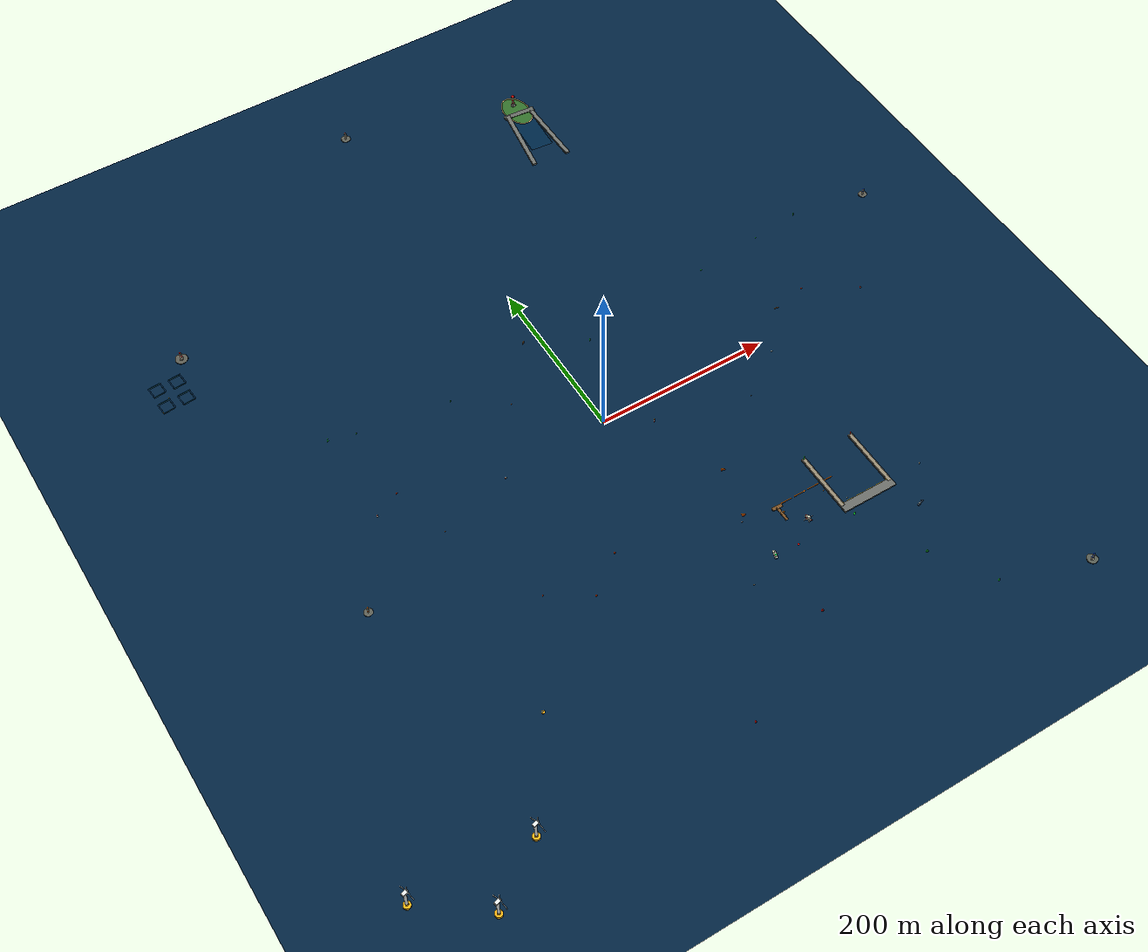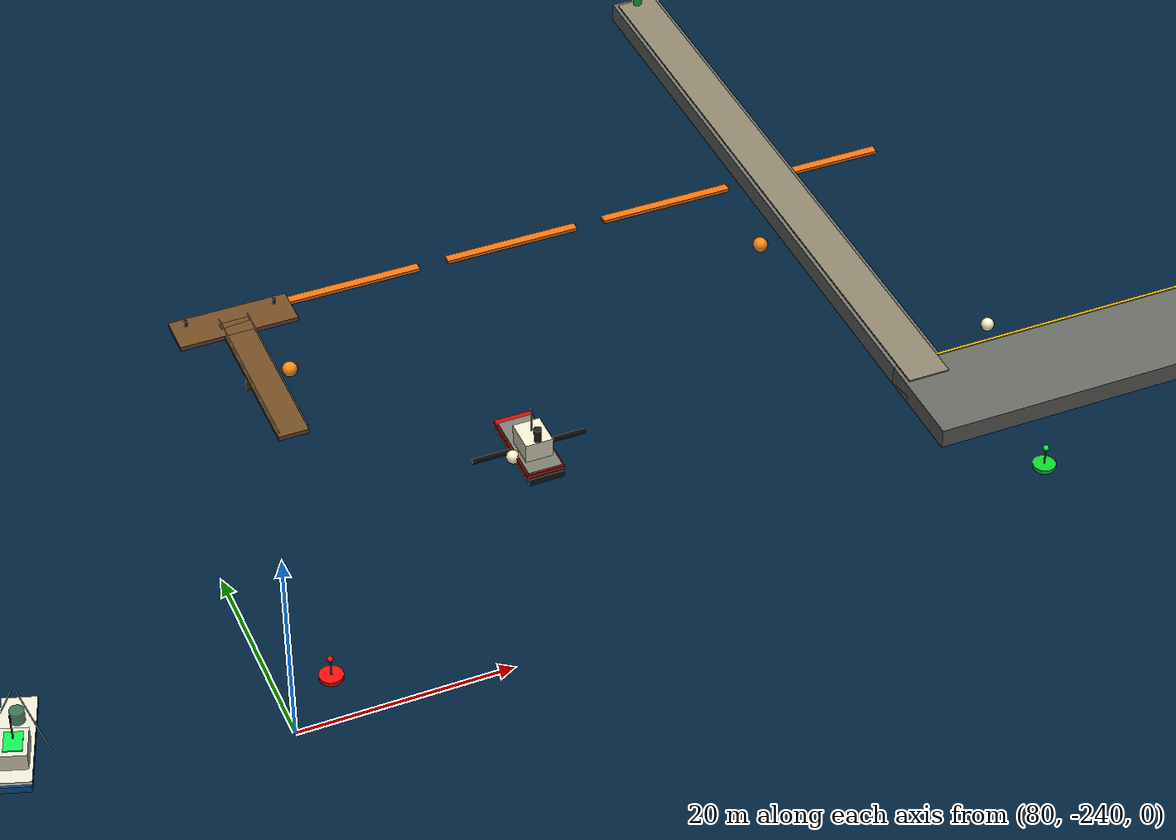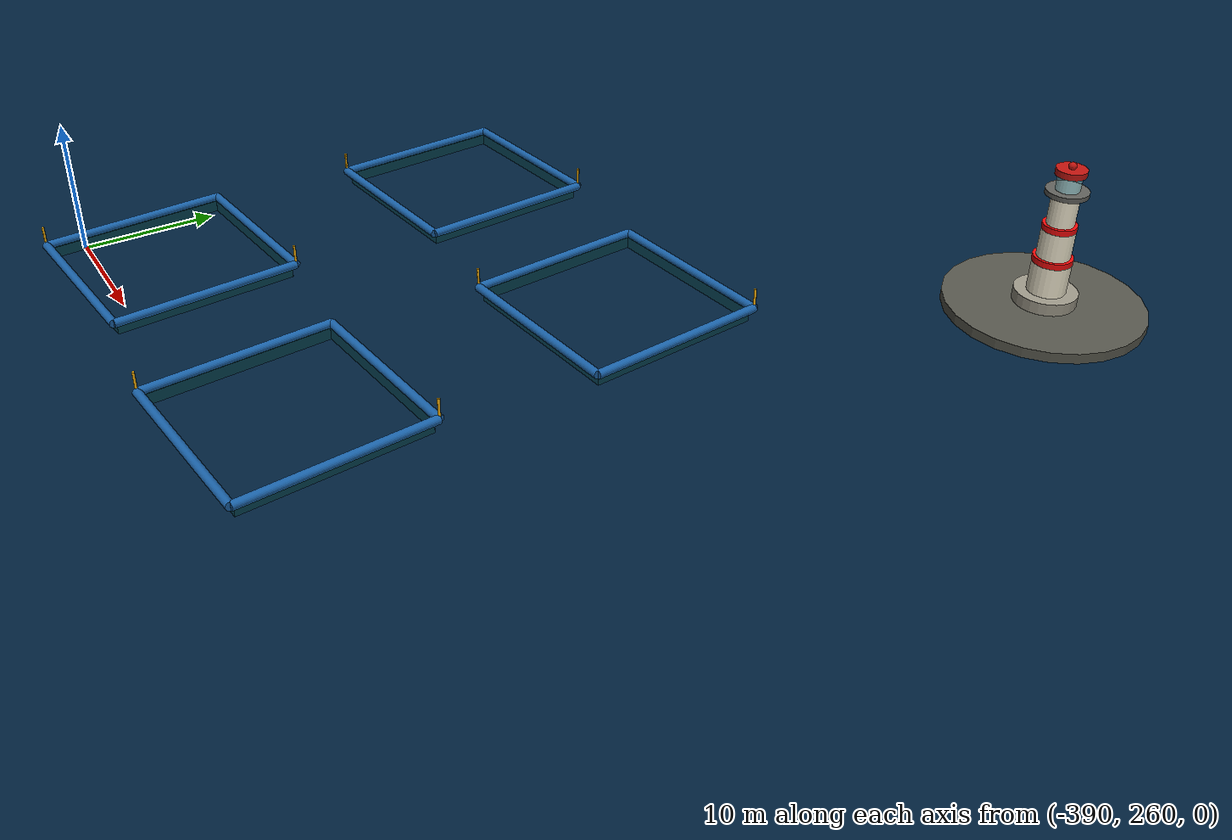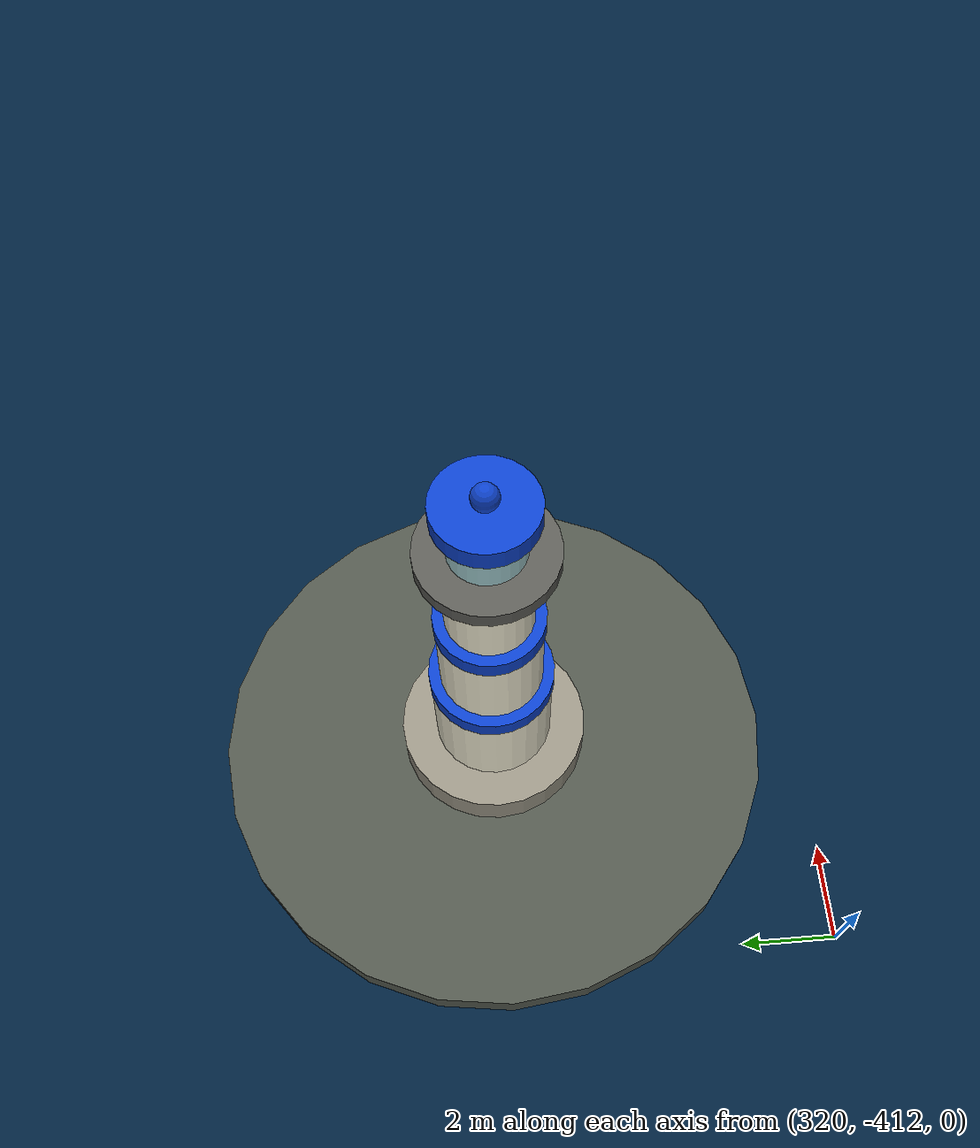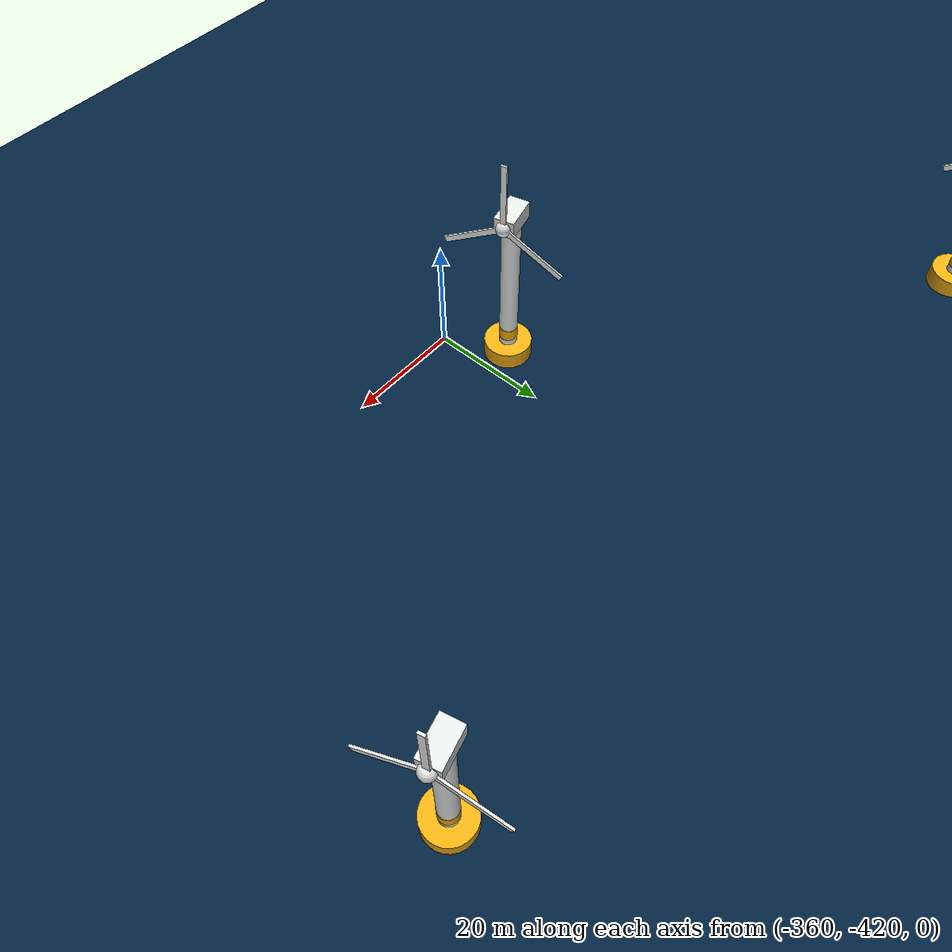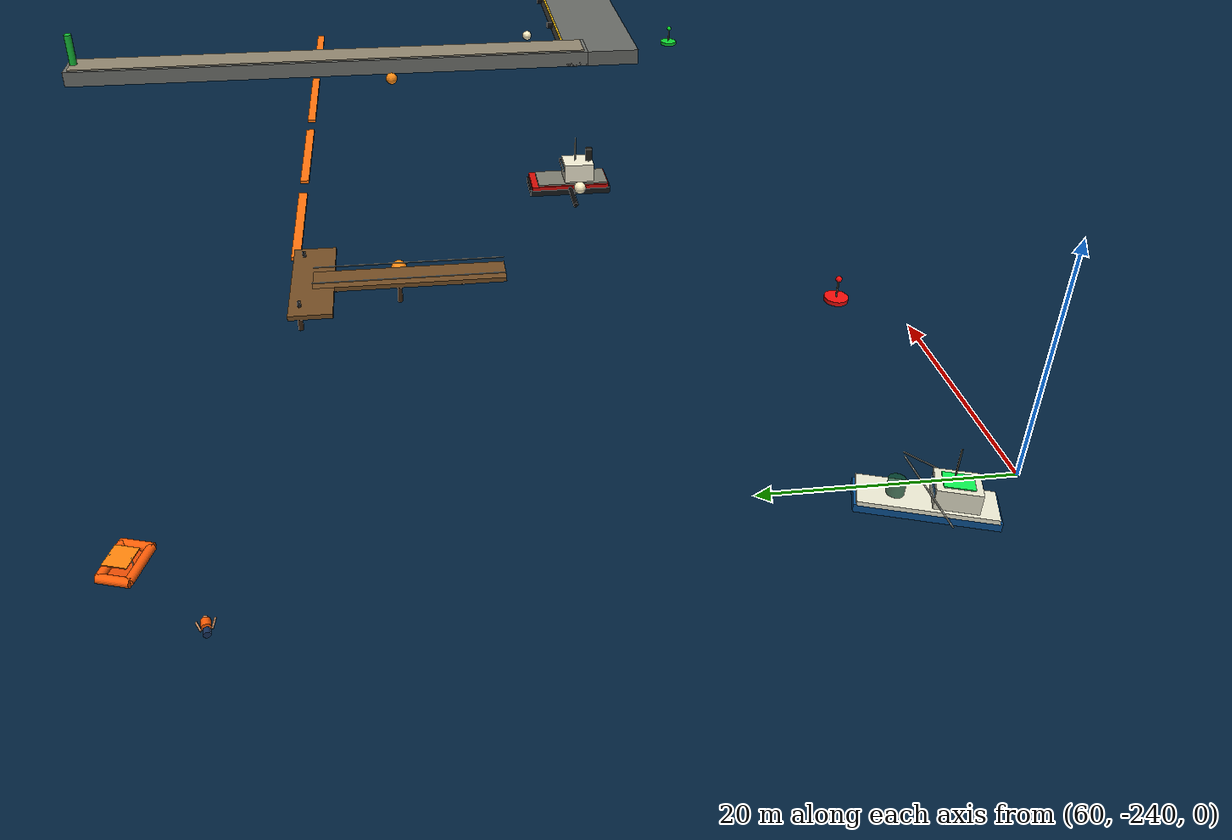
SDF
<sdf version="1.10">
 <world name="vrx_sydney_regatta_custom">
  <plugin filename="gz-sim-physics-system" name="gz::sim::systems::Physics"/>
  <plugin filename="gz-sim-user-commands-system" name="gz::sim::systems::UserCommands"/>
  <plugin filename="gz-sim-scene-broadcaster-system" name="gz::sim::systems::SceneBroadcaster"/>
  <plugin filename="gz-sim-contact-system" name="gz::sim::systems::Contact"/>
  <plugin filename="gz-sim-imu-system" name="gz::sim::systems::Imu"/>
  <plugin filename="gz-sim-navsat-system" name="gz::sim::systems::NavSat"/>
  <plugin filename="gz-sim-magnetometer-system" name="gz::sim::systems::Magnetometer"/>
  <plugin filename="gz-sim-sensors-system" name="gz::sim::systems::Sensors">
   <render_engine>ogre2</render_engine>
  </plugin>
  <plugin filename="gz-sim-particle-emitter-system" name="gz::sim::systems::ParticleEmitter"/>
  <plugin filename="gz-sim-wind-effects-system" name="gz::sim::systems::WindEffects">
   <force_approximation_scaling_factor>0.35</force_approximation_scaling_factor>
   <horizontal>
    <magnitude>
     <time_for_rise>12</time_for_rise>
     <sin><amplitude_percent>0.08</amplitude_percent><period>45</period></sin>
     <noise type="gaussian"><mean>0</mean><stddev>0.0004</stddev></noise>
    </magnitude>
    <direction>
     <time_for_rise>20</time_for_rise>
     <sin><amplitude>6</amplitude><period>60</period></sin>
     <noise type="gaussian"><mean>0</mean><stddev>0.025</stddev></noise>
    </direction>
   </horizontal>
   <vertical><noise type="gaussian"><mean>0</mean><stddev>0.015</stddev></noise></vertical>
  </plugin>
  <physics type="ode">
   <max_step_size>0.004</max_step_size>
   <real_time_factor>1</real_time_factor>
   <real_time_update_rate>250</real_time_update_rate>
  </physics>
  <gravity>0 0 -9.8</gravity>
  <magnetic_field>6.0e-06 2.3e-05 -4.2e-05</magnetic_field>
  <atmosphere type="adiabatic"/>
  <wind><linear_velocity>4 1.5 0</linear_velocity></wind>
  <scene>
   <grid>false</grid>
   <ambient>0.62 0.68 0.72 1</ambient>
   <background>0.70 0.82 0.95 1</background>
   <shadows>true</shadows>
   <fog>
    <type>linear</type>
    <color>0.70 0.82 0.95 1</color>
    <start>700</start>
    <end>3500</end>
    <density>0.0008</density>
   </fog>
  </scene>
  <spherical_coordinates>
   <surface_model>EARTH_WGS84</surface_model>
   <world_frame_orientation>ENU</world_frame_orientation>
   <latitude_deg>-33.722655</latitude_deg>
   <longitude_deg>150.674160</longitude_deg>
   <elevation>0</elevation>
   <heading_deg>0</heading_deg>
  </spherical_coordinates>
  <model name="ocean_collision_plane">
   <static>true</static>
   <link name="ocean_link">
    <visual name="ocean_backing_visual">
     <pose>0 0 -0.75 0 0 0</pose>
     <geometry><plane><normal>0 0 1</normal><size>12000 12000</size></plane></geometry>
     <material>
      <ambient>0.0 0.06 0.13 1</ambient>
      <diffuse>0.0 0.13 0.24 1</diffuse>
      <specular>0.02 0.04 0.05 1</specular>
      <emissive>0.0 0.015 0.035 1</emissive>
     </material>
    </visual>
    <collision name="ocean_collision">
     <geometry><plane><normal>0 0 1</normal><size>12000 12000</size></plane></geometry>
    </collision>
   </link>
  </model>
  <include><name>ocean_surface_details</name><uri>model://ocean_surface_details</uri></include>
  <include>
   <name>breakwater_harbor_island_lighthouse</name>
   <pose>152.84325 426.51996 6.88003 -0.01271 -0.01220 -1.64267</pose>
   <uri>model://breakwater_harbor_island_lighthouse</uri>
  </include>
  <include>
   <name>vrx_channel_red_west_outer</name>
   <pose>-260 20 0 0 0 0.25</pose>
   <uri>model://medium_buoy</uri>
  </include>
  <include>
   <name>vrx_channel_green_west_outer</name>
   <pose>-260 132 0 0 0 0.25</pose>
   <uri>model://green_channel_buoy</uri>
  </include>
  <include>
   <name>vrx_channel_red_mid_01</name>
   <pose>-125 -8 0 0 0 -0.15</pose>
   <uri>model://medium_buoy</uri>
  </include>
  <include>
   <name>vrx_channel_green_mid_01</name>
   <pose>-125 110 0 0 0 -0.15</pose>
   <uri>model://green_channel_buoy</uri>
  </include>
  <include>
   <name>vrx_channel_red_mid_02</name>
   <pose>45 -28 0 0 0 0.1</pose>
   <uri>model://medium_buoy</uri>
  </include>
  <include>
   <name>vrx_channel_green_mid_02</name>
   <pose>45 102 0 0 0 0.1</pose>
   <uri>model://green_channel_buoy</uri>
  </include>
  <include>
   <name>vrx_channel_red_east</name>
   <pose>205 -16 0 0 0 0.35</pose>
   <uri>model://medium_buoy</uri>
  </include>
  <include>
   <name>vrx_channel_green_east</name>
   <pose>205 122 0 0 0 0.35</pose>
   <uri>model://green_channel_buoy</uri>
  </include>
  <include>
   <name>vrx_channel_red_exit</name>
   <pose>342 6 0 0 0 -0.4</pose>
   <uri>model://medium_buoy</uri>
  </include>
  <include>
   <name>vrx_channel_green_exit</name>
   <pose>342 136 0 0 0 -0.4</pose>
   <uri>model://green_channel_buoy</uri>
  </include>
  <include>
   <name>vrx_aquaculture_cage_01</name>
   <pose>-385 265 0 0 0 0.08</pose>
   <uri>model://aquaculture_cage</uri>
  </include>
  <include>
   <name>vrx_aquaculture_cage_02</name>
   <pose>-362 265 0 0 0 0.08</pose>
   <uri>model://aquaculture_cage</uri>
  </include>
  <include>
   <name>vrx_aquaculture_cage_03</name>
   <pose>-385 290 0 0 0 0.08</pose>
   <uri>model://aquaculture_cage</uri>
  </include>
  <include>
   <name>vrx_aquaculture_cage_04</name>
   <pose>-362 290 0 0 0 0.08</pose>
   <uri>model://aquaculture_cage</uri>
  </include>
  <include>
   <name>vrx_floating_barrel_01</name>
   <pose>-210 -32 0 0 0 0.35</pose>
   <uri>model://floating_barrel</uri>
  </include>
  <include>
   <name>vrx_floating_barrel_02</name>
   <pose>-72 72 0 0 0 -0.7</pose>
   <uri>model://floating_barrel</uri>
  </include>
  <include>
   <name>vrx_floating_barrel_03</name>
   <pose>152 -54 0 0 0 1.1</pose>
   <uri>model://floating_barrel</uri>
  </include>
  <include><name>vrx_driftwood_01</name><pose>-18 138 0 0 0 0.65</pose><uri>model://driftwood</uri></include>
  <include><name>vrx_driftwood_02</name><pose>245 32 0 0 0 -0.45</pose><uri>model://driftwood</uri></include>
  <include>
   <name>vrx_abandoned_life_raft</name>
   <pose>72 -118 0 0 0 -0.35</pose>
   <uri>model://life_raft</uri>
  </include>
  <include>
   <name>vrx_service_marina_pier</name>
   <pose>92 -205 0 0 0 1.5708</pose>
   <uri>model://marina_pier</uri>
  </include>
  <include>
   <name>vrx_platform_breakwater</name>
   <pose>180 -222 0 0 0 1.5708</pose>
   <uri>model://harbor_breakwater</uri>
  </include>
  <include>
   <name>vrx_rescue_harbor_tug</name>
   <pose>112 -214 0 0 0 1.5708</pose>
   <uri>model://harbor_tug</uri>
  </include>
  <include>
   <name>vrx_coastal_fishing_boat</name>
   <pose>58 -232 0 0 0 1.25</pose>
   <uri>model://fishing_boat</uri>
  </include>
  <include>
   <name>vrx_rescue_casualty</name>
   <pose>52 -182 0 0 0 0.2</pose>
   <uri>model://person_overboard</uri>
  </include>
  <include>
   <name>vrx_rescue_life_raft</name>
   <pose>58 -176 0 0 0 -0.3</pose>
   <uri>model://life_raft</uri>
  </include>
  <include>
   <name>offshore_wind_turbine_west</name>
   <pose>-430 -360 0 0 0 0.25</pose>
   <uri>model://offshore_wind_turbine</uri>
  </include>
  <include>
   <name>offshore_wind_turbine_center</name>
   <pose>-365 -410 0 0 0 0.25</pose>
   <uri>model://offshore_wind_turbine</uri>
  </include>
  <include>
   <name>offshore_wind_turbine_east</name>
   <pose>-300 -365 0 0 0 0.25</pose>
   <uri>model://offshore_wind_turbine</uri>
  </include>
  <light name="sun" type="directional">
   <pose>0 0 10 0 0 0</pose>
   <diffuse>0.82 0.82 0.78 1</diffuse>
   <specular>0.25 0.25 0.22 1</specular>
   <attenuation>
    <range>1000</range>
    <constant>0.9</constant>
    <linear>0.01</linear>
    <quadratic>0.001</quadratic>
   </attenuation>
   <direction>-0.5 0.1 -0.9</direction>
  </light>
 </world>
</sdf>

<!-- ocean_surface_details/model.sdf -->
<sdf version="1.10">
  <model name="ocean_surface_details">
    <static>true</static>
    <link name="details">
      <collision name="red_marker_1_collision"><pose>85 -235 0.35 0 0 0</pose><geometry><cylinder><radius>1.1</radius><length>0.7</length></cylinder></geometry></collision>
      <visual name="red_marker_1_base"><pose>85 -235 0.20 0 0 0</pose><geometry><cylinder><radius>1.1</radius><length>0.4</length></cylinder></geometry><material><ambient>0.45 0.02 0.02 1</ambient><diffuse>0.95 0.05 0.04 1</diffuse></material></visual>
      <visual name="red_marker_1_mast"><pose>85 -235 1.25 0 0 0</pose><geometry><cylinder><radius>0.08</radius><length>1.8</length></cylinder></geometry><material><ambient>0.18 0.18 0.16 1</ambient><diffuse>0.45 0.45 0.40 1</diffuse></material></visual>
      <visual name="red_marker_1_top"><pose>85 -235 2.25 0 0 0</pose><geometry><sphere><radius>0.28</radius></sphere></geometry><material><ambient>0.7 0.02 0.02 1</ambient><diffuse>1 0.04 0.04 1</diffuse></material></visual>

      <collision name="green_marker_1_collision"><pose>155 -235 0.35 0 0 0</pose><geometry><cylinder><radius>1.1</radius><length>0.7</length></cylinder></geometry></collision>
      <visual name="green_marker_1_base"><pose>155 -235 0.20 0 0 0</pose><geometry><cylinder><radius>1.1</radius><length>0.4</length></cylinder></geometry><material><ambient>0.02 0.34 0.08 1</ambient><diffuse>0.04 0.82 0.18 1</diffuse></material></visual>
      <visual name="green_marker_1_mast"><pose>155 -235 1.25 0 0 0</pose><geometry><cylinder><radius>0.08</radius><length>1.8</length></cylinder></geometry><material><ambient>0.18 0.18 0.16 1</ambient><diffuse>0.45 0.45 0.40 1</diffuse></material></visual>
      <visual name="green_marker_1_top"><pose>155 -235 2.25 0 0 0</pose><geometry><sphere><radius>0.28</radius></sphere></geometry><material><ambient>0.02 0.6 0.1 1</ambient><diffuse>0.04 1 0.18 1</diffuse></material></visual>

      <collision name="red_marker_2_collision"><pose>60 -310 0.35 0 0 0</pose><geometry><cylinder><radius>1.1</radius><length>0.7</length></cylinder></geometry></collision>
      <visual name="red_marker_2_base"><pose>60 -310 0.20 0 0 0</pose><geometry><cylinder><radius>1.1</radius><length>0.4</length></cylinder></geometry><material><ambient>0.45 0.02 0.02 1</ambient><diffuse>0.95 0.05 0.04 1</diffuse></material></visual>
      <visual name="red_marker_2_mast"><pose>60 -310 1.25 0 0 0</pose><geometry><cylinder><radius>0.08</radius><length>1.8</length></cylinder></geometry><material><ambient>0.18 0.18 0.16 1</ambient><diffuse>0.45 0.45 0.40 1</diffuse></material></visual>
      <visual name="red_marker_2_top"><pose>60 -310 2.25 0 0 0</pose><geometry><sphere><radius>0.28</radius></sphere></geometry><material><ambient>0.7 0.02 0.02 1</ambient><diffuse>1 0.04 0.04 1</diffuse></material></visual>

      <collision name="green_marker_2_collision"><pose>190 -310 0.35 0 0 0</pose><geometry><cylinder><radius>1.1</radius><length>0.7</length></cylinder></geometry></collision>
      <visual name="green_marker_2_base"><pose>190 -310 0.20 0 0 0</pose><geometry><cylinder><radius>1.1</radius><length>0.4</length></cylinder></geometry><material><ambient>0.02 0.34 0.08 1</ambient><diffuse>0.04 0.82 0.18 1</diffuse></material></visual>
      <visual name="green_marker_2_mast"><pose>190 -310 1.25 0 0 0</pose><geometry><cylinder><radius>0.08</radius><length>1.8</length></cylinder></geometry><material><ambient>0.18 0.18 0.16 1</ambient><diffuse>0.45 0.45 0.40 1</diffuse></material></visual>
      <visual name="green_marker_2_top"><pose>190 -310 2.25 0 0 0</pose><geometry><sphere><radius>0.28</radius></sphere></geometry><material><ambient>0.02 0.6 0.1 1</ambient><diffuse>0.04 1 0.18 1</diffuse></material></visual>

      <visual name="weather_buoy_float"><pose>-230 -260 0.30 0 0 0</pose><geometry><cylinder><radius>1.8</radius><length>0.6</length></cylinder></geometry><material><ambient>0.78 0.48 0.03 1</ambient><diffuse>1.0 0.68 0.08 1</diffuse></material></visual>
      <visual name="weather_buoy_mast"><pose>-230 -260 2.0 0 0 0</pose><geometry><cylinder><radius>0.12</radius><length>3.0</length></cylinder></geometry><material><ambient>0.18 0.18 0.18 1</ambient><diffuse>0.50 0.50 0.47 1</diffuse></material></visual>
      <visual name="weather_buoy_sensor"><pose>-230 -260 3.65 0 0 0</pose><geometry><sphere><radius>0.45</radius></sphere></geometry><material><ambient>0.85 0.85 0.80 1</ambient><diffuse>1 1 0.92 1</diffuse></material></visual>
      <visual name="weather_buoy_solar_left"><pose>-231.1 -260 1.65 0 0.45 0</pose><geometry><box><size>1.6 0.08 0.75</size></box></geometry><material><ambient>0.02 0.08 0.14 1</ambient><diffuse>0.04 0.18 0.32 1</diffuse></material></visual>
      <visual name="weather_buoy_solar_right"><pose>-228.9 -260 1.65 0 -0.45 0</pose><geometry><box><size>1.6 0.08 0.75</size></box></geometry><material><ambient>0.02 0.08 0.14 1</ambient><diffuse>0.04 0.18 0.32 1</diffuse></material></visual>

      <visual name="mooring_buoy_1"><pose>95 -195 0.28 0 0 0</pose><geometry><sphere><radius>0.75</radius></sphere></geometry><material><ambient>0.86 0.42 0.02 1</ambient><diffuse>1.0 0.55 0.08 1</diffuse></material></visual>
      <visual name="mooring_buoy_2"><pose>145 -195 0.28 0 0 0</pose><geometry><sphere><radius>0.75</radius></sphere></geometry><material><ambient>0.86 0.42 0.02 1</ambient><diffuse>1.0 0.55 0.08 1</diffuse></material></visual>
      <visual name="mooring_buoy_3"><pose>110 -215 0.28 0 0 0</pose><geometry><sphere><radius>0.65</radius></sphere></geometry><material><ambient>0.92 0.88 0.74 1</ambient><diffuse>1.0 0.95 0.78 1</diffuse></material></visual>
      <visual name="mooring_buoy_4"><pose>160 -215 0.28 0 0 0</pose><geometry><sphere><radius>0.65</radius></sphere></geometry><material><ambient>0.92 0.88 0.74 1</ambient><diffuse>1.0 0.95 0.78 1</diffuse></material></visual>

      <visual name="safety_boom_1"><pose>105 -185 0.18 0 0 0</pose><geometry><box><size>14 0.9 0.35</size></box></geometry><material><ambient>0.9 0.32 0.02 1</ambient><diffuse>1.0 0.45 0.05 1</diffuse></material></visual>
      <visual name="safety_boom_2"><pose>122 -185 0.18 0 0 0</pose><geometry><box><size>14 0.9 0.35</size></box></geometry><material><ambient>0.9 0.32 0.02 1</ambient><diffuse>1.0 0.45 0.05 1</diffuse></material></visual>
      <visual name="safety_boom_3"><pose>139 -185 0.18 0 0 0</pose><geometry><box><size>14 0.9 0.35</size></box></geometry><material><ambient>0.9 0.32 0.02 1</ambient><diffuse>1.0 0.45 0.05 1</diffuse></material></visual>
      <visual name="safety_boom_4"><pose>156 -185 0.18 0 0 0</pose><geometry><box><size>14 0.9 0.35</size></box></geometry><material><ambient>0.9 0.32 0.02 1</ambient><diffuse>1.0 0.45 0.05 1</diffuse></material></visual>

      <visual name="service_skiff_hull"><pose>220 -260 0.28 0 0 0.35</pose><geometry><box><size>7.5 2.2 0.55</size></box></geometry><material><ambient>0.08 0.12 0.16 1</ambient><diffuse>0.16 0.25 0.34 1</diffuse></material></visual>
      <visual name="service_skiff_bow"><pose>223.4 -258.75 0.38 0 0 0.35</pose><geometry><sphere><radius>1.15</radius></sphere></geometry><material><ambient>0.08 0.12 0.16 1</ambient><diffuse>0.16 0.25 0.34 1</diffuse></material></visual>
      <visual name="service_skiff_cabin"><pose>219.2 -260.3 0.95 0 0 0.35</pose><geometry><box><size>1.8 1.4 0.95</size></box></geometry><material><ambient>0.70 0.78 0.78 1</ambient><diffuse>0.88 0.95 0.95 1</diffuse></material></visual>

      <collision name="west_lighthouse_collision"><pose>-345 315 5.9 0 0 0</pose><geometry><cylinder><radius>2.2</radius><length>11.8</length></cylinder></geometry></collision>
      <visual name="west_lighthouse_rock"><pose>-345 315 0.38 0 0 0</pose><geometry><cylinder><radius>7.0</radius><length>0.75</length></cylinder></geometry><material><ambient>0.18 0.18 0.16 1</ambient><diffuse>0.34 0.34 0.30 1</diffuse></material></visual>
      <visual name="west_lighthouse_plinth"><pose>-345 315 1.05 0 0 0</pose><geometry><cylinder><radius>2.2</radius><length>1.2</length></cylinder></geometry><material><ambient>0.35 0.33 0.30 1</ambient><diffuse>0.62 0.60 0.54 1</diffuse></material></visual>
      <visual name="west_lighthouse_lower"><pose>-345 315 3.0 0 0 0</pose><geometry><cylinder><radius>1.35</radius><length>2.7</length></cylinder></geometry><material><ambient>0.78 0.76 0.68 1</ambient><diffuse>0.95 0.92 0.82 1</diffuse></material></visual>
      <visual name="west_lighthouse_red_band_1"><pose>-345 315 4.15 0 0 0</pose><geometry><cylinder><radius>1.38</radius><length>0.45</length></cylinder></geometry><material><ambient>0.48 0.02 0.02 1</ambient><diffuse>0.95 0.04 0.04 1</diffuse></material></visual>
      <visual name="west_lighthouse_mid"><pose>-345 315 5.55 0 0 0</pose><geometry><cylinder><radius>1.16</radius><length>2.4</length></cylinder></geometry><material><ambient>0.78 0.76 0.68 1</ambient><diffuse>0.95 0.92 0.82 1</diffuse></material></visual>
      <visual name="west_lighthouse_red_band_2"><pose>-345 315 6.65 0 0 0</pose><geometry><cylinder><radius>1.18</radius><length>0.42</length></cylinder></geometry><material><ambient>0.48 0.02 0.02 1</ambient><diffuse>0.95 0.04 0.04 1</diffuse></material></visual>
      <visual name="west_lighthouse_upper"><pose>-345 315 8.0 0 0 0</pose><geometry><cylinder><radius>0.95</radius><length>2.3</length></cylinder></geometry><material><ambient>0.78 0.76 0.68 1</ambient><diffuse>0.95 0.92 0.82 1</diffuse></material></visual>
      <visual name="west_lighthouse_gallery"><pose>-345 315 9.25 0 0 0</pose><geometry><cylinder><radius>1.45</radius><length>0.35</length></cylinder></geometry><material><ambient>0.16 0.16 0.16 1</ambient><diffuse>0.38 0.38 0.36 1</diffuse></material></visual>
      <visual name="west_lighthouse_lantern"><pose>-345 315 10.0 0 0 0</pose><geometry><cylinder><radius>0.82</radius><length>1.15</length></cylinder></geometry><material><ambient>0.55 0.72 0.74 0.68</ambient><diffuse>0.70 0.95 0.98 0.68</diffuse></material></visual>
      <visual name="west_lighthouse_roof"><pose>-345 315 10.75 0 0 0</pose><geometry><cylinder><radius>1.05</radius><length>0.45</length></cylinder></geometry><material><ambient>0.42 0.04 0.03 1</ambient><diffuse>0.76 0.08 0.06 1</diffuse></material></visual>
      <visual name="west_lighthouse_cap"><pose>-345 315 11.15 0 0 0</pose><geometry><sphere><radius>0.28</radius></sphere></geometry><material><ambient>0.42 0.04 0.03 1</ambient><diffuse>0.76 0.08 0.06 1</diffuse></material></visual>

      <collision name="south_lighthouse_collision"><pose>325 -405 5.4 0 0 0</pose><geometry><cylinder><radius>2.0</radius><length>10.8</length></cylinder></geometry></collision>
      <visual name="south_lighthouse_rock"><pose>325 -405 0.35 0 0 0</pose><geometry><cylinder><radius>6.0</radius><length>0.7</length></cylinder></geometry><material><ambient>0.17 0.18 0.16 1</ambient><diffuse>0.32 0.34 0.30 1</diffuse></material></visual>
      <visual name="south_lighthouse_plinth"><pose>325 -405 0.95 0 0 0</pose><geometry><cylinder><radius>2.0</radius><length>1.1</length></cylinder></geometry><material><ambient>0.34 0.32 0.29 1</ambient><diffuse>0.60 0.58 0.52 1</diffuse></material></visual>
      <visual name="south_lighthouse_lower"><pose>325 -405 2.75 0 0 0</pose><geometry><cylinder><radius>1.25</radius><length>2.5</length></cylinder></geometry><material><ambient>0.80 0.78 0.70 1</ambient><diffuse>0.96 0.94 0.84 1</diffuse></material></visual>
      <visual name="south_lighthouse_blue_band_1"><pose>325 -405 3.85 0 0 0</pose><geometry><cylinder><radius>1.28</radius><length>0.40</length></cylinder></geometry><material><ambient>0.02 0.14 0.42 1</ambient><diffuse>0.05 0.26 0.80 1</diffuse></material></visual>
      <visual name="south_lighthouse_mid"><pose>325 -405 5.15 0 0 0</pose><geometry><cylinder><radius>1.05</radius><length>2.2</length></cylinder></geometry><material><ambient>0.80 0.78 0.70 1</ambient><diffuse>0.96 0.94 0.84 1</diffuse></material></visual>
      <visual name="south_lighthouse_blue_band_2"><pose>325 -405 6.15 0 0 0</pose><geometry><cylinder><radius>1.08</radius><length>0.40</length></cylinder></geometry><material><ambient>0.02 0.14 0.42 1</ambient><diffuse>0.05 0.26 0.80 1</diffuse></material></visual>
      <visual name="south_lighthouse_upper"><pose>325 -405 7.35 0 0 0</pose><geometry><cylinder><radius>0.86</radius><length>2.0</length></cylinder></geometry><material><ambient>0.80 0.78 0.70 1</ambient><diffuse>0.96 0.94 0.84 1</diffuse></material></visual>
      <visual name="south_lighthouse_gallery"><pose>325 -405 8.48 0 0 0</pose><geometry><cylinder><radius>1.30</radius><length>0.32</length></cylinder></geometry><material><ambient>0.15 0.15 0.15 1</ambient><diffuse>0.36 0.36 0.34 1</diffuse></material></visual>
      <visual name="south_lighthouse_lantern"><pose>325 -405 9.15 0 0 0</pose><geometry><cylinder><radius>0.72</radius><length>1.0</length></cylinder></geometry><material><ambient>0.55 0.72 0.74 0.68</ambient><diffuse>0.70 0.95 0.98 0.68</diffuse></material></visual>
      <visual name="south_lighthouse_roof"><pose>325 -405 9.80 0 0 0</pose><geometry><cylinder><radius>0.95</radius><length>0.42</length></cylinder></geometry><material><ambient>0.02 0.14 0.42 1</ambient><diffuse>0.05 0.26 0.80 1</diffuse></material></visual>
      <visual name="south_lighthouse_cap"><pose>325 -405 10.18 0 0 0</pose><geometry><sphere><radius>0.25</radius></sphere></geometry><material><ambient>0.02 0.14 0.42 1</ambient><diffuse>0.05 0.26 0.80 1</diffuse></material></visual>

      <visual name="outer_red_marker_3_base"><pose>-65 -375 0.22 0 0 0</pose><geometry><cylinder><radius>1.05</radius><length>0.44</length></cylinder></geometry><material><ambient>0.45 0.02 0.02 1</ambient><diffuse>0.95 0.05 0.04 1</diffuse></material></visual>
      <visual name="outer_red_marker_3_mast"><pose>-65 -375 1.45 0 0 0</pose><geometry><cylinder><radius>0.09</radius><length>2.1</length></cylinder></geometry><material><ambient>0.18 0.18 0.16 1</ambient><diffuse>0.45 0.45 0.40 1</diffuse></material></visual>
      <visual name="outer_red_marker_3_top"><pose>-65 -375 2.7 0 0 0</pose><geometry><box><size>0.62 0.62 0.62</size></box></geometry><material><ambient>0.7 0.02 0.02 1</ambient><diffuse>1 0.04 0.04 1</diffuse></material></visual>
      <visual name="outer_green_marker_3_base"><pose>230 -375 0.22 0 0 0</pose><geometry><cylinder><radius>1.05</radius><length>0.44</length></cylinder></geometry><material><ambient>0.02 0.34 0.08 1</ambient><diffuse>0.04 0.82 0.18 1</diffuse></material></visual>
      <visual name="outer_green_marker_3_mast"><pose>230 -375 1.45 0 0 0</pose><geometry><cylinder><radius>0.09</radius><length>2.1</length></cylinder></geometry><material><ambient>0.18 0.18 0.16 1</ambient><diffuse>0.45 0.45 0.40 1</diffuse></material></visual>
      <visual name="outer_green_marker_3_top"><pose>230 -375 2.7 0 0 0</pose><geometry><sphere><radius>0.36</radius></sphere></geometry><material><ambient>0.02 0.6 0.1 1</ambient><diffuse>0.04 1 0.18 1</diffuse></material></visual>

      <visual name="reef_warning_float_1"><pose>-165 -150 0.32 0 0 0</pose><geometry><sphere><radius>0.82</radius></sphere></geometry><material><ambient>0.86 0.18 0.02 1</ambient><diffuse>1.0 0.26 0.04 1</diffuse></material></visual>
      <visual name="reef_warning_float_2"><pose>-120 -178 0.32 0 0 0</pose><geometry><sphere><radius>0.82</radius></sphere></geometry><material><ambient>0.86 0.18 0.02 1</ambient><diffuse>1.0 0.26 0.04 1</diffuse></material></visual>
      <visual name="reef_warning_float_3"><pose>-78 -145 0.32 0 0 0</pose><geometry><sphere><radius>0.82</radius></sphere></geometry><material><ambient>0.86 0.18 0.02 1</ambient><diffuse>1.0 0.26 0.04 1</diffuse></material></visual>
      <visual name="white_mooring_float_5"><pose>20 -250 0.26 0 0 0</pose><geometry><sphere><radius>0.62</radius></sphere></geometry><material><ambient>0.92 0.88 0.74 1</ambient><diffuse>1.0 0.95 0.78 1</diffuse></material></visual>
      <visual name="white_mooring_float_6"><pose>250 -220 0.26 0 0 0</pose><geometry><sphere><radius>0.62</radius></sphere></geometry><material><ambient>0.92 0.88 0.74 1</ambient><diffuse>1.0 0.95 0.78 1</diffuse></material></visual>

      <collision name="north_lighthouse_collision"><pose>-40 520 4.75 0 0 0</pose><geometry><cylinder><radius>1.6</radius><length>9.5</length></cylinder></geometry></collision>
      <visual name="north_lighthouse_rock"><pose>-40 520 0.32 0 0 0</pose><geometry><cylinder><radius>5.5</radius><length>0.64</length></cylinder></geometry><material><ambient>0.17 0.18 0.16 1</ambient><diffuse>0.34 0.35 0.31 1</diffuse></material></visual>
      <visual name="north_lighthouse_tower"><pose>-40 520 4.6 0 0 0</pose><geometry><cylinder><radius>1.05</radius><length>7.7</length></cylinder></geometry><material><ambient>0.82 0.80 0.72 1</ambient><diffuse>0.98 0.95 0.84 1</diffuse></material></visual>
      <visual name="north_lighthouse_band_lower"><pose>-40 520 3.15 0 0 0</pose><geometry><cylinder><radius>1.08</radius><length>0.45</length></cylinder></geometry><material><ambient>0.52 0.04 0.03 1</ambient><diffuse>0.95 0.07 0.05 1</diffuse></material></visual>
      <visual name="north_lighthouse_band_upper"><pose>-40 520 5.85 0 0 0</pose><geometry><cylinder><radius>1.08</radius><length>0.45</length></cylinder></geometry><material><ambient>0.52 0.04 0.03 1</ambient><diffuse>0.95 0.07 0.05 1</diffuse></material></visual>
      <visual name="north_lighthouse_gallery"><pose>-40 520 8.65 0 0 0</pose><geometry><cylinder><radius>1.35</radius><length>0.3</length></cylinder></geometry><material><ambient>0.16 0.16 0.15 1</ambient><diffuse>0.38 0.38 0.35 1</diffuse></material></visual>
      <visual name="north_lighthouse_lantern"><pose>-40 520 9.25 0 0 0</pose><geometry><cylinder><radius>0.72</radius><length>0.9</length></cylinder></geometry><material><ambient>0.60 0.76 0.78 0.7</ambient><diffuse>0.76 0.98 1.0 0.7</diffuse></material></visual>
      <visual name="north_lighthouse_roof"><pose>-40 520 9.9 0 0 0</pose><geometry><cylinder><radius>0.95</radius><length>0.38</length></cylinder></geometry><material><ambient>0.52 0.04 0.03 1</ambient><diffuse>0.85 0.07 0.05 1</diffuse></material></visual>

      <collision name="east_lighthouse_collision"><pose>430 120 4.35 0 0 0</pose><geometry><cylinder><radius>1.55</radius><length>8.7</length></cylinder></geometry></collision>
      <visual name="east_lighthouse_rock"><pose>430 120 0.30 0 0 0</pose><geometry><cylinder><radius>5.0</radius><length>0.6</length></cylinder></geometry><material><ambient>0.18 0.18 0.16 1</ambient><diffuse>0.34 0.34 0.30 1</diffuse></material></visual>
      <visual name="east_lighthouse_tower"><pose>430 120 4.25 0 0 0</pose><geometry><cylinder><radius>0.98</radius><length>7.1</length></cylinder></geometry><material><ambient>0.80 0.78 0.70 1</ambient><diffuse>0.96 0.94 0.84 1</diffuse></material></visual>
      <visual name="east_lighthouse_blue_band_lower"><pose>430 120 2.9 0 0 0</pose><geometry><cylinder><radius>1.01</radius><length>0.42</length></cylinder></geometry><material><ambient>0.02 0.14 0.42 1</ambient><diffuse>0.06 0.28 0.82 1</diffuse></material></visual>
      <visual name="east_lighthouse_blue_band_upper"><pose>430 120 5.35 0 0 0</pose><geometry><cylinder><radius>1.01</radius><length>0.42</length></cylinder></geometry><material><ambient>0.02 0.14 0.42 1</ambient><diffuse>0.06 0.28 0.82 1</diffuse></material></visual>
      <visual name="east_lighthouse_gallery"><pose>430 120 7.95 0 0 0</pose><geometry><cylinder><radius>1.25</radius><length>0.3</length></cylinder></geometry><material><ambient>0.16 0.16 0.15 1</ambient><diffuse>0.38 0.38 0.35 1</diffuse></material></visual>
      <visual name="east_lighthouse_lantern"><pose>430 120 8.5 0 0 0</pose><geometry><cylinder><radius>0.68</radius><length>0.85</length></cylinder></geometry><material><ambient>0.60 0.76 0.78 0.7</ambient><diffuse>0.76 0.98 1.0 0.7</diffuse></material></visual>
      <visual name="east_lighthouse_roof"><pose>430 120 9.1 0 0 0</pose><geometry><cylinder><radius>0.9</radius><length>0.35</length></cylinder></geometry><material><ambient>0.02 0.14 0.42 1</ambient><diffuse>0.06 0.28 0.82 1</diffuse></material></visual>

      <collision name="river_entry_lighthouse_collision"><pose>-320 -75 4.15 0 0 0</pose><geometry><cylinder><radius>1.45</radius><length>8.3</length></cylinder></geometry></collision>
      <visual name="river_entry_lighthouse_rock"><pose>-320 -75 0.28 0 0 0</pose><geometry><cylinder><radius>4.8</radius><length>0.56</length></cylinder></geometry><material><ambient>0.17 0.18 0.16 1</ambient><diffuse>0.34 0.35 0.31 1</diffuse></material></visual>
      <visual name="river_entry_lighthouse_tower"><pose>-320 -75 4.05 0 0 0</pose><geometry><cylinder><radius>0.92</radius><length>6.8</length></cylinder></geometry><material><ambient>0.82 0.80 0.72 1</ambient><diffuse>0.98 0.95 0.84 1</diffuse></material></visual>
      <visual name="river_entry_lighthouse_orange_band_lower"><pose>-320 -75 2.75 0 0 0</pose><geometry><cylinder><radius>0.95</radius><length>0.40</length></cylinder></geometry><material><ambient>0.72 0.28 0.02 1</ambient><diffuse>1.0 0.43 0.04 1</diffuse></material></visual>
      <visual name="river_entry_lighthouse_orange_band_upper"><pose>-320 -75 5.1 0 0 0</pose><geometry><cylinder><radius>0.95</radius><length>0.40</length></cylinder></geometry><material><ambient>0.72 0.28 0.02 1</ambient><diffuse>1.0 0.43 0.04 1</diffuse></material></visual>
      <visual name="river_entry_lighthouse_gallery"><pose>-320 -75 7.6 0 0 0</pose><geometry><cylinder><radius>1.18</radius><length>0.28</length></cylinder></geometry><material><ambient>0.16 0.16 0.15 1</ambient><diffuse>0.38 0.38 0.35 1</diffuse></material></visual>
      <visual name="river_entry_lighthouse_lantern"><pose>-320 -75 8.1 0 0 0</pose><geometry><cylinder><radius>0.62</radius><length>0.8</length></cylinder></geometry><material><ambient>0.60 0.76 0.78 0.7</ambient><diffuse>0.76 0.98 1.0 0.7</diffuse></material></visual>
      <visual name="river_entry_lighthouse_roof"><pose>-320 -75 8.68 0 0 0</pose><geometry><cylinder><radius>0.82</radius><length>0.34</length></cylinder></geometry><material><ambient>0.72 0.28 0.02 1</ambient><diffuse>1.0 0.43 0.04 1</diffuse></material></visual>

      <visual name="new_buoy_1_float"><pose>-230 35 0.30 0 0 0</pose><geometry><sphere><radius>0.78</radius></sphere></geometry><material><ambient>0.80 0.12 0.02 1</ambient><diffuse>1.0 0.18 0.04 1</diffuse></material></visual>
      <visual name="new_buoy_1_mast"><pose>-230 35 1.25 0 0 0</pose><geometry><cylinder><radius>0.06</radius><length>1.55</length></cylinder></geometry><material><ambient>0.18 0.18 0.16 1</ambient><diffuse>0.45 0.45 0.40 1</diffuse></material></visual>
      <visual name="new_buoy_2_float"><pose>-230 125 0.30 0 0 0</pose><geometry><sphere><radius>0.78</radius></sphere></geometry><material><ambient>0.02 0.42 0.08 1</ambient><diffuse>0.04 0.95 0.18 1</diffuse></material></visual>
      <visual name="new_buoy_2_mast"><pose>-230 125 1.25 0 0 0</pose><geometry><cylinder><radius>0.06</radius><length>1.55</length></cylinder></geometry><material><ambient>0.18 0.18 0.16 1</ambient><diffuse>0.45 0.45 0.40 1</diffuse></material></visual>
      <visual name="new_buoy_3_float"><pose>285 40 0.30 0 0 0</pose><geometry><sphere><radius>0.78</radius></sphere></geometry><material><ambient>0.80 0.12 0.02 1</ambient><diffuse>1.0 0.18 0.04 1</diffuse></material></visual>
      <visual name="new_buoy_3_mast"><pose>285 40 1.25 0 0 0</pose><geometry><cylinder><radius>0.06</radius><length>1.55</length></cylinder></geometry><material><ambient>0.18 0.18 0.16 1</ambient><diffuse>0.45 0.45 0.40 1</diffuse></material></visual>
      <visual name="new_buoy_4_float"><pose>285 130 0.30 0 0 0</pose><geometry><sphere><radius>0.78</radius></sphere></geometry><material><ambient>0.02 0.42 0.08 1</ambient><diffuse>0.04 0.95 0.18 1</diffuse></material></visual>
      <visual name="new_buoy_4_mast"><pose>285 130 1.25 0 0 0</pose><geometry><cylinder><radius>0.06</radius><length>1.55</length></cylinder></geometry><material><ambient>0.18 0.18 0.16 1</ambient><diffuse>0.45 0.45 0.40 1</diffuse></material></visual>

      <light name="red_marker_light" type="point"><pose>85 -235 2.6 0 0 0</pose><cast_shadows>false</cast_shadows><intensity>1.1</intensity><diffuse>1 0.05 0.03 1</diffuse><attenuation><range>45</range><constant>0.8</constant><linear>0.04</linear><quadratic>0.002</quadratic></attenuation></light>
      <light name="green_marker_light" type="point"><pose>155 -235 2.6 0 0 0</pose><cast_shadows>false</cast_shadows><intensity>1.1</intensity><diffuse>0.05 1 0.12 1</diffuse><attenuation><range>45</range><constant>0.8</constant><linear>0.04</linear><quadratic>0.002</quadratic></attenuation></light>
      <light name="weather_buoy_light" type="point"><pose>-230 -260 4.15 0 0 0</pose><cast_shadows>false</cast_shadows><intensity>1.0</intensity><diffuse>1 0.82 0.25 1</diffuse><attenuation><range>55</range><constant>0.8</constant><linear>0.035</linear><quadratic>0.0015</quadratic></attenuation></light>
      <light name="west_lighthouse_beacon" type="point"><pose>-345 315 10.15 0 0 0</pose><cast_shadows>false</cast_shadows><intensity>2.8</intensity><diffuse>1 0.88 0.55 1</diffuse><attenuation><range>130</range><constant>0.65</constant><linear>0.018</linear><quadratic>0.0006</quadratic></attenuation></light>
      <light name="south_lighthouse_beacon" type="point"><pose>325 -405 9.25 0 0 0</pose><cast_shadows>false</cast_shadows><intensity>2.4</intensity><diffuse>0.55 0.74 1 1</diffuse><attenuation><range>120</range><constant>0.65</constant><linear>0.02</linear><quadratic>0.0007</quadratic></attenuation></light>
      <light name="outer_red_marker_light" type="point"><pose>-65 -375 2.95 0 0 0</pose><cast_shadows>false</cast_shadows><intensity>0.9</intensity><diffuse>1 0.05 0.03 1</diffuse><attenuation><range>42</range><constant>0.8</constant><linear>0.04</linear><quadratic>0.002</quadratic></attenuation></light>
      <light name="outer_green_marker_light" type="point"><pose>230 -375 2.95 0 0 0</pose><cast_shadows>false</cast_shadows><intensity>0.9</intensity><diffuse>0.05 1 0.12 1</diffuse><attenuation><range>42</range><constant>0.8</constant><linear>0.04</linear><quadratic>0.002</quadratic></attenuation></light>
      <light name="north_lighthouse_beacon" type="point"><pose>-40 520 9.3 0 0 0</pose><cast_shadows>false</cast_shadows><intensity>2.4</intensity><diffuse>1 0.88 0.55 1</diffuse><attenuation><range>120</range><constant>0.65</constant><linear>0.02</linear><quadratic>0.0007</quadratic></attenuation></light>
      <light name="east_lighthouse_beacon" type="point"><pose>430 120 8.55 0 0 0</pose><cast_shadows>false</cast_shadows><intensity>2.2</intensity><diffuse>0.55 0.74 1 1</diffuse><attenuation><range>110</range><constant>0.65</constant><linear>0.02</linear><quadratic>0.0008</quadratic></attenuation></light>
      <light name="river_entry_lighthouse_beacon" type="point"><pose>-320 -75 8.15 0 0 0</pose><cast_shadows>false</cast_shadows><intensity>2.0</intensity><diffuse>1 0.62 0.22 1</diffuse><attenuation><range>105</range><constant>0.65</constant><linear>0.02</linear><quadratic>0.0008</quadratic></attenuation></light>
      <light name="new_buoy_1_light" type="point"><pose>-230 35 1.9 0 0 0</pose><cast_shadows>false</cast_shadows><intensity>0.7</intensity><diffuse>1 0.05 0.03 1</diffuse><attenuation><range>34</range><constant>0.8</constant><linear>0.05</linear><quadratic>0.0025</quadratic></attenuation></light>
      <light name="new_buoy_2_light" type="point"><pose>-230 125 1.9 0 0 0</pose><cast_shadows>false</cast_shadows><intensity>0.7</intensity><diffuse>0.05 1 0.12 1</diffuse><attenuation><range>34</range><constant>0.8</constant><linear>0.05</linear><quadratic>0.0025</quadratic></attenuation></light>
      <light name="new_buoy_3_light" type="point"><pose>285 40 1.9 0 0 0</pose><cast_shadows>false</cast_shadows><intensity>0.7</intensity><diffuse>1 0.05 0.03 1</diffuse><attenuation><range>34</range><constant>0.8</constant><linear>0.05</linear><quadratic>0.0025</quadratic></attenuation></light>
      <light name="new_buoy_4_light" type="point"><pose>285 130 1.9 0 0 0</pose><cast_shadows>false</cast_shadows><intensity>0.7</intensity><diffuse>0.05 1 0.12 1</diffuse><attenuation><range>34</range><constant>0.8</constant><linear>0.05</linear><quadratic>0.0025</quadratic></attenuation></light>
    </link>
  </model>
</sdf>

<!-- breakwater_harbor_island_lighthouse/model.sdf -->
<sdf version="1.10">
  <model name="breakwater_harbor_island_lighthouse">
    <static>true</static>
    <link name="harbor_island">
      <collision name="island_collision"><pose>-20 0 0.65 0 0 0.15</pose><geometry><ellipsoid><radii>24 15 1.45</radii></ellipsoid></geometry></collision>
      <visual name="island_visual"><pose>-20 0 0.35 0 0 0.15</pose><geometry><ellipsoid><radii>24 15 1.35</radii></ellipsoid></geometry><material><ambient>0.11 0.24 0.09 1</ambient><diffuse>0.19 0.42 0.16 1</diffuse></material></visual>
      <visual name="sand_ring"><pose>-20 0 0.42 0 0 0.15</pose><geometry><ellipsoid><radii>25 16 0.18</radii></ellipsoid></geometry><material><ambient>0.52 0.43 0.26 1</ambient><diffuse>0.78 0.66 0.42 1</diffuse></material></visual>

      <collision name="north_breakwater_collision"><pose>28 18 1.1 0 0 0.08</pose><geometry><box><size>88 5 2.2</size></box></geometry></collision>
      <collision name="south_breakwater_collision"><pose>28 -18 1.1 0 0 -0.08</pose><geometry><box><size>88 5 2.2</size></box></geometry></collision>
      <collision name="quay_collision"><pose>-14 0 1.1 0 0 0</pose><geometry><box><size>6 38 2.2</size></box></geometry></collision>
      <visual name="north_breakwater"><pose>28 18 1.1 0 0 0.08</pose><geometry><box><size>88 5 2.2</size></box></geometry><material><ambient>0.25 0.26 0.25 1</ambient><diffuse>0.42 0.43 0.41 1</diffuse></material></visual>
      <visual name="south_breakwater"><pose>28 -18 1.1 0 0 -0.08</pose><geometry><box><size>88 5 2.2</size></box></geometry><material><ambient>0.25 0.26 0.25 1</ambient><diffuse>0.42 0.43 0.41 1</diffuse></material></visual>
      <visual name="quay"><pose>-14 0 1.1 0 0 0</pose><geometry><box><size>6 38 2.2</size></box></geometry><material><ambient>0.22 0.23 0.22 1</ambient><diffuse>0.38 0.39 0.37 1</diffuse></material></visual>
      <visual name="harbor_water_hint"><pose>20 0 0.05 0 0 0</pose><geometry><box><size>56 27 0.05</size></box></geometry><material><ambient>0.0 0.09 0.18 0.55</ambient><diffuse>0.0 0.18 0.32 0.55</diffuse></material></visual>

      <collision name="lighthouse_base_collision"><pose>-30 0 1.65 0 0 0</pose><geometry><cylinder><radius>3.2</radius><length>1.0</length></cylinder></geometry></collision>
      <visual name="lighthouse_base"><pose>-30 0 1.65 0 0 0</pose><geometry><cylinder><radius>3.2</radius><length>1.0</length></cylinder></geometry><material><ambient>0.18 0.18 0.17 1</ambient><diffuse>0.32 0.32 0.30 1</diffuse></material></visual>
      <collision name="lighthouse_tower_collision"><pose>-30 0 8.0 0 0 0</pose><geometry><cylinder><radius>1.15</radius><length>12.2</length></cylinder></geometry></collision>
      <visual name="lighthouse_tower"><pose>-30 0 8.0 0 0 0</pose><geometry><cylinder><radius>1.15</radius><length>12.2</length></cylinder></geometry><material><ambient>0.86 0.84 0.76 1</ambient><diffuse>0.96 0.94 0.84 1</diffuse></material></visual>
      <visual name="lighthouse_red_band_low"><pose>-30 0 5.2 0 0 0</pose><geometry><cylinder><radius>1.2</radius><length>0.75</length></cylinder></geometry><material><ambient>0.55 0.02 0.02 1</ambient><diffuse>0.86 0.04 0.035 1</diffuse></material></visual>
      <visual name="lighthouse_red_band_high"><pose>-30 0 9.3 0 0 0</pose><geometry><cylinder><radius>1.2</radius><length>0.75</length></cylinder></geometry><material><ambient>0.55 0.02 0.02 1</ambient><diffuse>0.86 0.04 0.035 1</diffuse></material></visual>
      <visual name="lantern_room"><pose>-30 0 14.45 0 0 0</pose><geometry><cylinder><radius>1.55</radius><length>1.1</length></cylinder></geometry><material><ambient>0.92 0.78 0.28 0.85</ambient><diffuse>1 0.88 0.42 0.85</diffuse></material></visual>
      <visual name="lighthouse_roof"><pose>-30 0 15.25 0 0 0</pose><geometry><cylinder><radius>1.85</radius><length>0.55</length></cylinder></geometry><material><ambient>0.45 0.02 0.02 1</ambient><diffuse>0.72 0.03 0.03 1</diffuse></material></visual>

      <light name="lighthouse_beacon" type="point"><pose>-30 0 14.55 0 0 0</pose><cast_shadows>false</cast_shadows><intensity>5.0</intensity><diffuse>1 0.88 0.42 1</diffuse><specular>1 0.92 0.65 1</specular><attenuation><range>220</range><constant>0.45</constant><linear>0.012</linear><quadratic>0.00025</quadratic></attenuation></light>
      <light name="green_harbor_light" type="point"><pose>70 18 4.2 0 0 0</pose><cast_shadows>false</cast_shadows><intensity>2.2</intensity><diffuse>0.05 1 0.22 1</diffuse><attenuation><range>70</range><constant>0.65</constant><linear>0.025</linear><quadratic>0.0008</quadratic></attenuation></light>
      <light name="red_harbor_light" type="point"><pose>70 -18 4.2 0 0 0</pose><cast_shadows>false</cast_shadows><intensity>2.2</intensity><diffuse>1 0.05 0.025 1</diffuse><attenuation><range>70</range><constant>0.65</constant><linear>0.025</linear><quadratic>0.0008</quadratic></attenuation></light>
    </link>
  </model>
</sdf>

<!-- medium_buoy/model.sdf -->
<sdf version="1.8">
  <model name="medium_buoy">
    <link name="body">
      <inertial>
        <mass>140</mass>
        <inertia><ixx>65</ixx><iyy>65</iyy><izz>22</izz></inertia>
      </inertial>
      <collision name="base_collision">
        <pose>0 0 0.45 0 0 0</pose>
        <geometry>
          <cylinder>
            <radius>0.7</radius>
            <length>0.9</length>
          </cylinder>
        </geometry>
      </collision>

      <collision name="mast_collision">
        <pose>0 0 2.55 0 0 0</pose>
        <geometry>
          <cylinder>
            <radius>0.11</radius>
            <length>3.3</length>
          </cylinder>
        </geometry>
      </collision>

      <collision name="daymark_lower_collision">
        <pose>0 0 2.0 0 0 0</pose>
        <geometry>
          <box>
            <size>1.05 0.12 0.65</size>
          </box>
        </geometry>
      </collision>

      <collision name="daymark_upper_collision">
        <pose>0 0 3.1 0 0 1.5708</pose>
        <geometry>
          <box>
            <size>1.05 0.12 0.65</size>
          </box>
        </geometry>
      </collision>

      <visual name="base_float">
        <pose>0 0 0.45 0 0 0</pose>
        <geometry>
          <cylinder>
            <radius>0.72</radius>
            <length>0.9</length>
          </cylinder>
        </geometry>
        <material>
          <ambient>0.65 0.05 0.04 1</ambient>
          <diffuse>0.92 0.07 0.05 1</diffuse>
          <specular>0.25 0.04 0.04 1</specular>
        </material>
      </visual>

      <visual name="white_band">
        <pose>0 0 0.82 0 0 0</pose>
        <geometry>
          <cylinder>
            <radius>0.73</radius>
            <length>0.16</length>
          </cylinder>
        </geometry>
        <material>
          <ambient>0.92 0.9 0.82 1</ambient>
          <diffuse>1 0.98 0.88 1</diffuse>
          <specular>0.45 0.45 0.4 1</specular>
        </material>
      </visual>

      <visual name="tower_mast">
        <pose>0 0 2.55 0 0 0</pose>
        <geometry>
          <cylinder>
            <radius>0.08</radius>
            <length>3.3</length>
          </cylinder>
        </geometry>
        <material>
          <ambient>0.04 0.04 0.04 1</ambient>
          <diffuse>0.06 0.06 0.06 1</diffuse>
          <specular>0.2 0.2 0.2 1</specular>
        </material>
      </visual>

      <visual name="daymark_lower">
        <pose>0 0 2.0 0 0 0</pose>
        <geometry>
          <box>
            <size>0.95 0.08 0.55</size>
          </box>
        </geometry>
        <material>
          <ambient>0.85 0.1 0.06 1</ambient>
          <diffuse>1 0.15 0.08 1</diffuse>
          <specular>0.3 0.05 0.03 1</specular>
        </material>
      </visual>

      <visual name="daymark_upper">
        <pose>0 0 3.1 0 0 1.5708</pose>
        <geometry>
          <box>
            <size>0.95 0.08 0.55</size>
          </box>
        </geometry>
        <material>
          <ambient>0.85 0.1 0.06 1</ambient>
          <diffuse>1 0.15 0.08 1</diffuse>
          <specular>0.3 0.05 0.03 1</specular>
        </material>
      </visual>

      <visual name="top_beacon">
        <pose>0 0 4.35 0 0 0</pose>
        <geometry>
          <sphere>
            <radius>0.22</radius>
          </sphere>
        </geometry>
        <material>
          <ambient>1 0.78 0.1 1</ambient>
          <diffuse>1 0.86 0.15 1</diffuse>
          <specular>1 0.9 0.35 1</specular>
        </material>
      </visual>

      <light name="buoy_light" type="point">
        <pose>0 0 4.35 0 0 0</pose>
        <cast_shadows>false</cast_shadows>
        <intensity>1.2</intensity>
        <diffuse>1 0.78 0.1 1</diffuse>
        <specular>1 0.86 0.25 1</specular>
        <attenuation>
          <range>25</range>
          <constant>0.7</constant>
          <linear>0.04</linear>
          <quadratic>0.002</quadratic>
        </attenuation>
      </light>
    </link>
    <plugin filename="libBoatWaveFollower.so" name="gz::sim::systems::BoatWaveFollower">
      <mean_z>0</mean_z><heave_amplitude>0.08</heave_amplitude>
      <roll_amplitude>0.045</roll_amplitude><pitch_amplitude>0.038</pitch_amplitude>
      <primary_frequency>0.9</primary_frequency><secondary_frequency>1.45</secondary_frequency>
      <wave_number_x>0.2</wave_number_x><wave_number_y>0.16</wave_number_y>
    </plugin>
  </model>
</sdf>

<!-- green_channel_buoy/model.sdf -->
<sdf version="1.10">
  <model name="green_channel_buoy">
    <link name="body">
      <inertial><mass>140</mass><inertia><ixx>65</ixx><iyy>65</iyy><izz>22</izz></inertia></inertial>
      <collision name="float_collision"><pose>0 0 0.45 0 0 0</pose><geometry><cylinder><radius>0.65</radius><length>0.9</length></cylinder></geometry></collision>
      <collision name="mast_collision"><pose>0 0 2.15 0 0 0</pose><geometry><cylinder><radius>0.1</radius><length>2.7</length></cylinder></geometry></collision>
      <visual name="float"><pose>0 0 0.45 0 0 0</pose><geometry><cylinder><radius>0.68</radius><length>0.9</length></cylinder></geometry><material><ambient>0.02 0.42 0.12 1</ambient><diffuse>0.03 0.72 0.2 1</diffuse><specular>0.2 0.3 0.2 1</specular></material></visual>
      <visual name="reflective_band"><pose>0 0 0.78 0 0 0</pose><geometry><cylinder><radius>0.69</radius><length>0.14</length></cylinder></geometry><material><ambient>0.85 0.88 0.75 1</ambient><diffuse>1 1 0.86 1</diffuse><emissive>0.15 0.15 0.1 1</emissive></material></visual>
      <visual name="mast"><pose>0 0 2.15 0 0 0</pose><geometry><cylinder><radius>0.075</radius><length>2.7</length></cylinder></geometry><material><ambient>0.02 0.25 0.07 1</ambient><diffuse>0.03 0.5 0.12 1</diffuse></material></visual>
      <visual name="topmark"><pose>0 0 3.45 0 0 0</pose><geometry><cone><radius>0.38</radius><length>0.75</length></cone></geometry><material><ambient>0.02 0.36 0.1 1</ambient><diffuse>0.03 0.68 0.18 1</diffuse></material></visual>
      <visual name="lantern"><pose>0 0 3.95 0 0 0</pose><geometry><sphere><radius>0.18</radius></sphere></geometry><material><ambient>0.08 0.8 0.2 1</ambient><diffuse>0.1 1 0.25 1</diffuse><emissive>0.05 0.8 0.16 1</emissive></material></visual>
      <light name="green_light" type="point"><pose>0 0 3.95 0 0 0</pose><cast_shadows>false</cast_shadows><intensity>1.4</intensity><diffuse>0.08 1 0.22 1</diffuse><specular>0.1 1 0.3 1</specular><attenuation><range>28</range><constant>0.7</constant><linear>0.04</linear><quadratic>0.002</quadratic></attenuation></light>
    </link>
    <plugin filename="libBoatWaveFollower.so" name="gz::sim::systems::BoatWaveFollower"><mean_z>0</mean_z><heave_amplitude>0.08</heave_amplitude><roll_amplitude>0.045</roll_amplitude><pitch_amplitude>0.038</pitch_amplitude><primary_frequency>0.9</primary_frequency><secondary_frequency>1.45</secondary_frequency><wave_number_x>0.2</wave_number_x><wave_number_y>0.16</wave_number_y></plugin>
  </model>
</sdf>

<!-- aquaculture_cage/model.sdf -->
<sdf version="1.10">
  <model name="aquaculture_cage">
    <link name="cage">
      <inertial><mass>450</mass><inertia><ixx>5500</ixx><iyy>5500</iyy><izz>8200</izz></inertia></inertial>
      <collision name="north_float_collision"><pose>0 7 0.25 0 1.5708 0</pose><geometry><cylinder><radius>0.3</radius><length>14</length></cylinder></geometry></collision>
      <collision name="south_float_collision"><pose>0 -7 0.25 0 1.5708 0</pose><geometry><cylinder><radius>0.3</radius><length>14</length></cylinder></geometry></collision>
      <collision name="east_float_collision"><pose>7 0 0.25 1.5708 0 0</pose><geometry><cylinder><radius>0.3</radius><length>14</length></cylinder></geometry></collision>
      <collision name="west_float_collision"><pose>-7 0 0.25 1.5708 0 0</pose><geometry><cylinder><radius>0.3</radius><length>14</length></cylinder></geometry></collision>
      <visual name="north_float"><pose>0 7 0.25 0 1.5708 0</pose><geometry><cylinder><radius>0.32</radius><length>14</length></cylinder></geometry><material><ambient>0.08 0.2 0.34 1</ambient><diffuse>0.1 0.38 0.65 1</diffuse><specular>0.3 0.35 0.4 1</specular></material></visual>
      <visual name="south_float"><pose>0 -7 0.25 0 1.5708 0</pose><geometry><cylinder><radius>0.32</radius><length>14</length></cylinder></geometry><material><ambient>0.08 0.2 0.34 1</ambient><diffuse>0.1 0.38 0.65 1</diffuse></material></visual>
      <visual name="east_float"><pose>7 0 0.25 1.5708 0 0</pose><geometry><cylinder><radius>0.32</radius><length>14</length></cylinder></geometry><material><ambient>0.08 0.2 0.34 1</ambient><diffuse>0.1 0.38 0.65 1</diffuse></material></visual>
      <visual name="west_float"><pose>-7 0 0.25 1.5708 0 0</pose><geometry><cylinder><radius>0.32</radius><length>14</length></cylinder></geometry><material><ambient>0.08 0.2 0.34 1</ambient><diffuse>0.1 0.38 0.65 1</diffuse></material></visual>
      <visual name="net_bottom"><pose>0 0 -3.8 0 0 0</pose><geometry><box><size>13.5 13.5 0.03</size></box></geometry><material><ambient>0.02 0.14 0.11 0.35</ambient><diffuse>0.03 0.3 0.22 0.35</diffuse></material></visual>
      <visual name="net_north"><pose>0 6.75 -1.8 0 0 0</pose><geometry><box><size>13.5 0.03 4</size></box></geometry><material><ambient>0.02 0.16 0.12 0.38</ambient><diffuse>0.03 0.34 0.24 0.38</diffuse></material></visual>
      <visual name="net_south"><pose>0 -6.75 -1.8 0 0 0</pose><geometry><box><size>13.5 0.03 4</size></box></geometry><material><ambient>0.02 0.16 0.12 0.38</ambient><diffuse>0.03 0.34 0.24 0.38</diffuse></material></visual>
      <visual name="net_east"><pose>6.75 0 -1.8 0 0 0</pose><geometry><box><size>0.03 13.5 4</size></box></geometry><material><ambient>0.02 0.16 0.12 0.38</ambient><diffuse>0.03 0.34 0.24 0.38</diffuse></material></visual>
      <visual name="net_west"><pose>-6.75 0 -1.8 0 0 0</pose><geometry><box><size>0.03 13.5 4</size></box></geometry><material><ambient>0.02 0.16 0.12 0.38</ambient><diffuse>0.03 0.34 0.24 0.38</diffuse></material></visual>
      <visual name="corner_marker_ne"><pose>7 7 1.05 0 0 0</pose><geometry><cylinder><radius>0.09</radius><length>1.5</length></cylinder></geometry><material><ambient>0.85 0.55 0.02 1</ambient><diffuse>1 0.72 0.05 1</diffuse></material></visual>
      <visual name="corner_marker_sw"><pose>-7 -7 1.05 0 0 0</pose><geometry><cylinder><radius>0.09</radius><length>1.5</length></cylinder></geometry><material><ambient>0.85 0.55 0.02 1</ambient><diffuse>1 0.72 0.05 1</diffuse></material></visual>
      <light name="cage_light_ne" type="point"><pose>7 7 1.8 0 0 0</pose><cast_shadows>false</cast_shadows><intensity>0.8</intensity><diffuse>1 0.72 0.08 1</diffuse><attenuation><range>18</range><constant>0.8</constant><linear>0.06</linear><quadratic>0.003</quadratic></attenuation></light>
      <light name="cage_light_sw" type="point"><pose>-7 -7 1.8 0 0 0</pose><cast_shadows>false</cast_shadows><intensity>0.8</intensity><diffuse>1 0.72 0.08 1</diffuse><attenuation><range>18</range><constant>0.8</constant><linear>0.06</linear><quadratic>0.003</quadratic></attenuation></light>
    </link>
    <plugin filename="libBoatWaveFollower.so" name="gz::sim::systems::BoatWaveFollower"><mean_z>0</mean_z><heave_amplitude>0.05</heave_amplitude><roll_amplitude>0.012</roll_amplitude><pitch_amplitude>0.012</pitch_amplitude><primary_frequency>0.75</primary_frequency><secondary_frequency>1.2</secondary_frequency><wave_number_x>0.12</wave_number_x><wave_number_y>0.1</wave_number_y></plugin>
  </model>
</sdf>

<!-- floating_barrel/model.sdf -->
<sdf version="1.10"><model name="floating_barrel"><link name="barrel">
  <inertial><mass>35</mass><inertia><ixx>4</ixx><iyy>8</iyy><izz>8</izz></inertia></inertial>
  <collision name="collision"><pose>0 0 0 0 1.5708 0</pose><geometry><cylinder><radius>0.32</radius><length>0.9</length></cylinder></geometry></collision>
  <visual name="body"><pose>0 0 0 0 1.5708 0</pose><geometry><cylinder><radius>0.33</radius><length>0.9</length></cylinder></geometry><material><ambient>0.42 0.18 0.03 1</ambient><diffuse>0.72 0.3 0.04 1</diffuse><specular>0.24 0.18 0.12 1</specular></material></visual>
  <visual name="band_a"><pose>-0.34 0 0 0 1.5708 0</pose><geometry><cylinder><radius>0.345</radius><length>0.07</length></cylinder></geometry><material><ambient>0.09 0.09 0.08 1</ambient><diffuse>0.18 0.18 0.16 1</diffuse></material></visual>
  <visual name="band_b"><pose>0.34 0 0 0 1.5708 0</pose><geometry><cylinder><radius>0.345</radius><length>0.07</length></cylinder></geometry><material><ambient>0.09 0.09 0.08 1</ambient><diffuse>0.18 0.18 0.16 1</diffuse></material></visual>
  <visual name="oil_stain"><pose>0 0.05 -0.28 0 0 0</pose><geometry><ellipsoid><radii>0.75 0.5 0.025</radii></ellipsoid></geometry><material><ambient>0.015 0.02 0.025 0.55</ambient><diffuse>0.025 0.035 0.04 0.55</diffuse><specular>0.7 0.65 0.6 1</specular></material></visual>
  </link><plugin filename="libBoatWaveFollower.so" name="gz::sim::systems::BoatWaveFollower"><mean_z>0.18</mean_z><heave_amplitude>0.1</heave_amplitude><roll_amplitude>0.18</roll_amplitude><pitch_amplitude>0.15</pitch_amplitude><primary_frequency>1.05</primary_frequency><secondary_frequency>1.7</secondary_frequency></plugin></model></sdf>

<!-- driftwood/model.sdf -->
<sdf version="1.10"><model name="driftwood"><link name="timber">
  <inertial><mass>55</mass><inertia><ixx>6</ixx><iyy>70</iyy><izz>72</izz></inertia></inertial>
  <collision name="log_collision"><pose>0 0 0 0 1.5708 0</pose><geometry><cylinder><radius>0.22</radius><length>4.8</length></cylinder></geometry></collision>
  <collision name="plank_collision"><pose>0.5 0.7 0.08 0.05 0.08 -0.3</pose><geometry><box><size>3.2 0.48 0.16</size></box></geometry></collision>
  <visual name="log"><pose>0 0 0 0 1.5708 0</pose><geometry><cylinder><radius>0.23</radius><length>4.8</length></cylinder></geometry><material><ambient>0.19 0.11 0.055 1</ambient><diffuse>0.36 0.21 0.09 1</diffuse><specular>0.05 0.04 0.03 1</specular></material></visual>
  <visual name="bark_strip"><pose>0 0.17 0.12 0 0 0</pose><geometry><box><size>3.7 0.09 0.06</size></box></geometry><material><ambient>0.08 0.05 0.025 1</ambient><diffuse>0.15 0.09 0.04 1</diffuse></material></visual>
  <visual name="plank_a"><pose>0.5 0.7 0.08 0.05 0.08 -0.3</pose><geometry><box><size>3.2 0.48 0.16</size></box></geometry><material><ambient>0.27 0.18 0.09 1</ambient><diffuse>0.5 0.34 0.16 1</diffuse></material></visual>
  <visual name="plank_b"><pose>-0.6 -0.65 0.05 -0.04 0.06 0.22</pose><geometry><box><size>2.6 0.42 0.14</size></box></geometry><material><ambient>0.24 0.16 0.08 1</ambient><diffuse>0.44 0.29 0.13 1</diffuse></material></visual>
  </link><plugin filename="libBoatWaveFollower.so" name="gz::sim::systems::BoatWaveFollower"><mean_z>0.1</mean_z><heave_amplitude>0.09</heave_amplitude><roll_amplitude>0.13</roll_amplitude><pitch_amplitude>0.1</pitch_amplitude><primary_frequency>1</primary_frequency><secondary_frequency>1.55</secondary_frequency></plugin></model></sdf>

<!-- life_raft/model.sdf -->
<sdf version="1.10"><model name="life_raft"><link name="raft">
  <inertial><mass>85</mass><inertia><ixx>70</ixx><iyy>95</iyy><izz>130</izz></inertia></inertial>
  <collision name="collision"><pose>0 0 0.28 0 0 0</pose><geometry><box><size>3.6 2.4 0.55</size></box></geometry></collision>
  <visual name="floor"><pose>0 0 0.16 0 0 0</pose><geometry><box><size>3.1 1.9 0.18</size></box></geometry><material><ambient>0.55 0.15 0.01 1</ambient><diffuse>0.92 0.3 0.015 1</diffuse></material></visual>
  <visual name="tube_front"><pose>1.65 0 0.38 1.5708 0 0</pose><geometry><cylinder><radius>0.34</radius><length>2.4</length></cylinder></geometry><material><ambient>0.82 0.2 0.01 1</ambient><diffuse>1 0.36 0.02 1</diffuse><specular>0.25 0.2 0.15 1</specular></material></visual>
  <visual name="tube_rear"><pose>-1.65 0 0.38 1.5708 0 0</pose><geometry><cylinder><radius>0.34</radius><length>2.4</length></cylinder></geometry><material><ambient>0.82 0.2 0.01 1</ambient><diffuse>1 0.36 0.02 1</diffuse></material></visual>
  <visual name="tube_left"><pose>0 1.05 0.38 0 1.5708 0</pose><geometry><cylinder><radius>0.34</radius><length>3.3</length></cylinder></geometry><material><ambient>0.82 0.2 0.01 1</ambient><diffuse>1 0.36 0.02 1</diffuse></material></visual>
  <visual name="tube_right"><pose>0 -1.05 0.38 0 1.5708 0</pose><geometry><cylinder><radius>0.34</radius><length>3.3</length></cylinder></geometry><material><ambient>0.82 0.2 0.01 1</ambient><diffuse>1 0.36 0.02 1</diffuse></material></visual>
  <visual name="canopy"><pose>-0.35 0 1.25 0 0 0</pose><geometry><box><size>1.9 1.8 0.08</size></box></geometry><material><ambient>0.85 0.32 0.02 0.9</ambient><diffuse>1 0.52 0.04 0.9</diffuse></material></visual>
  <visual name="canopy_pole_left"><pose>-0.35 0.78 0.85 0 0 0</pose><geometry><cylinder><radius>0.035</radius><length>0.9</length></cylinder></geometry><material><ambient>0.8 0.8 0.75 1</ambient><diffuse>0.95 0.95 0.9 1</diffuse></material></visual>
  <visual name="canopy_pole_right"><pose>-0.35 -0.78 0.85 0 0 0</pose><geometry><cylinder><radius>0.035</radius><length>0.9</length></cylinder></geometry><material><ambient>0.8 0.8 0.75 1</ambient><diffuse>0.95 0.95 0.9 1</diffuse></material></visual>
  </link><plugin filename="libBoatWaveFollower.so" name="gz::sim::systems::BoatWaveFollower"><mean_z>0.12</mean_z><heave_amplitude>0.12</heave_amplitude><roll_amplitude>0.09</roll_amplitude><pitch_amplitude>0.075</pitch_amplitude><primary_frequency>0.9</primary_frequency><secondary_frequency>1.45</secondary_frequency></plugin></model></sdf>

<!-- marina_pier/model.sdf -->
<sdf version="1.10"><model name="marina_pier"><static>true</static><link name="pier">
  <collision name="walkway_collision"><pose>9 0 1 0 0 0</pose><geometry><box><size>18 3 0.45</size></box></geometry></collision>
  <collision name="head_collision"><pose>18 0 1 0 0 0</pose><geometry><box><size>4 12 0.45</size></box></geometry></collision>
  <visual name="walkway"><pose>9 0 1 0 0 0</pose><geometry><box><size>18 3 0.45</size></box></geometry><material><ambient>0.23 0.15 0.075 1</ambient><diffuse>0.45 0.3 0.14 1</diffuse><specular>0.05 0.04 0.03 1</specular></material></visual>
  <visual name="head"><pose>18 0 1 0 0 0</pose><geometry><box><size>4 12 0.45</size></box></geometry><material><ambient>0.23 0.15 0.075 1</ambient><diffuse>0.45 0.3 0.14 1</diffuse></material></visual>
  <visual name="pile_a"><pose>4 -1.25 -0.8 0 0 0</pose><geometry><cylinder><radius>0.22</radius><length>4</length></cylinder></geometry><material><ambient>0.12 0.08 0.04 1</ambient><diffuse>0.24 0.15 0.07 1</diffuse></material></visual>
  <visual name="pile_b"><pose>10 1.25 -0.8 0 0 0</pose><geometry><cylinder><radius>0.22</radius><length>4</length></cylinder></geometry><material><ambient>0.12 0.08 0.04 1</ambient><diffuse>0.24 0.15 0.07 1</diffuse></material></visual>
  <visual name="pile_c"><pose>16 -1.25 -0.8 0 0 0</pose><geometry><cylinder><radius>0.22</radius><length>4</length></cylinder></geometry><material><ambient>0.12 0.08 0.04 1</ambient><diffuse>0.24 0.15 0.07 1</diffuse></material></visual>
  <visual name="pile_d"><pose>19 5 -0.8 0 0 0</pose><geometry><cylinder><radius>0.24</radius><length>4</length></cylinder></geometry><material><ambient>0.12 0.08 0.04 1</ambient><diffuse>0.24 0.15 0.07 1</diffuse></material></visual>
  <visual name="pile_e"><pose>19 -5 -0.8 0 0 0</pose><geometry><cylinder><radius>0.24</radius><length>4</length></cylinder></geometry><material><ambient>0.12 0.08 0.04 1</ambient><diffuse>0.24 0.15 0.07 1</diffuse></material></visual>
  <visual name="rail_left"><pose>9 1.42 1.75 0 0 0</pose><geometry><box><size>18 0.07 0.08</size></box></geometry><material><ambient>0.45 0.46 0.45 1</ambient><diffuse>0.7 0.72 0.7 1</diffuse><specular>0.4 0.4 0.4 1</specular></material></visual>
  <visual name="rail_right"><pose>9 -1.42 1.75 0 0 0</pose><geometry><box><size>18 0.07 0.08</size></box></geometry><material><ambient>0.45 0.46 0.45 1</ambient><diffuse>0.7 0.72 0.7 1</diffuse></material></visual>
  <visual name="bollard_n"><pose>19 4.5 1.5 0 0 0</pose><geometry><cylinder><radius>0.16</radius><length>0.55</length></cylinder></geometry><material><ambient>0.08 0.08 0.08 1</ambient><diffuse>0.15 0.15 0.15 1</diffuse></material></visual>
  <visual name="bollard_s"><pose>19 -4.5 1.5 0 0 0</pose><geometry><cylinder><radius>0.16</radius><length>0.55</length></cylinder></geometry><material><ambient>0.08 0.08 0.08 1</ambient><diffuse>0.15 0.15 0.15 1</diffuse></material></visual>
  <light name="pier_light_n" type="point"><pose>19 5 2.2 0 0 0</pose><cast_shadows>false</cast_shadows><intensity>1</intensity><diffuse>1 0.75 0.2 1</diffuse><attenuation><range>22</range><constant>0.8</constant><linear>0.05</linear><quadratic>0.003</quadratic></attenuation></light>
  <light name="pier_light_s" type="point"><pose>19 -5 2.2 0 0 0</pose><cast_shadows>false</cast_shadows><intensity>1</intensity><diffuse>1 0.75 0.2 1</diffuse><attenuation><range>22</range><constant>0.8</constant><linear>0.05</linear><quadratic>0.003</quadratic></attenuation></light>
  </link></model></sdf>

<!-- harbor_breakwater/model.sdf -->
<sdf version="1.10"><model name="harbor_breakwater"><static>true</static><link name="harbor">
  <collision name="north_arm_collision"><pose>35 30 1 0 0 0</pose><geometry><box><size>70 5 2</size></box></geometry></collision>
  <collision name="south_arm_collision"><pose>35 -30 1 0 0 0</pose><geometry><box><size>70 5 2</size></box></geometry></collision>
  <collision name="quay_collision"><pose>-2 0 1 0 0 0</pose><geometry><box><size>10 65 2</size></box></geometry></collision>
  <visual name="north_arm"><pose>35 30 1 0 0 0</pose><geometry><box><size>70 5 2</size></box></geometry><material><ambient>0.27 0.28 0.27 1</ambient><diffuse>0.43 0.44 0.42 1</diffuse><specular>0.06 0.06 0.06 1</specular></material></visual>
  <visual name="south_arm"><pose>35 -30 1 0 0 0</pose><geometry><box><size>70 5 2</size></box></geometry><material><ambient>0.27 0.28 0.27 1</ambient><diffuse>0.43 0.44 0.42 1</diffuse></material></visual>
  <visual name="quay"><pose>-2 0 1 0 0 0</pose><geometry><box><size>10 65 2</size></box></geometry><material><ambient>0.24 0.25 0.24 1</ambient><diffuse>0.4 0.41 0.39 1</diffuse></material></visual>
  <visual name="north_walkway"><pose>35 30 2.08 0 0 0</pose><geometry><box><size>69 4.2 0.16</size></box></geometry><material><ambient>0.38 0.35 0.29 1</ambient><diffuse>0.56 0.52 0.43 1</diffuse></material></visual>
  <visual name="south_walkway"><pose>35 -30 2.08 0 0 0</pose><geometry><box><size>69 4.2 0.16</size></box></geometry><material><ambient>0.38 0.35 0.29 1</ambient><diffuse>0.56 0.52 0.43 1</diffuse></material></visual>
  <visual name="quay_hazard_line"><pose>3.05 0 2.08 0 0 0</pose><geometry><box><size>0.25 62 0.12</size></box></geometry><material><ambient>0.95 0.67 0.02 1</ambient><diffuse>1 0.78 0.04 1</diffuse></material></visual>
  <visual name="north_beacon_tower"><pose>69 30 4.2 0 0 0</pose><geometry><cylinder><radius>0.48</radius><length>4.2</length></cylinder></geometry><material><ambient>0.06 0.42 0.13 1</ambient><diffuse>0.08 0.75 0.22 1</diffuse></material></visual>
  <visual name="south_beacon_tower"><pose>69 -30 4.2 0 0 0</pose><geometry><cylinder><radius>0.48</radius><length>4.2</length></cylinder></geometry><material><ambient>0.58 0.04 0.025 1</ambient><diffuse>0.9 0.06 0.035 1</diffuse></material></visual>
  <visual name="fender_01"><pose>3.2 18 1 0 1.5708 0</pose><geometry><cylinder><radius>0.42</radius><length>1.2</length></cylinder></geometry><material><ambient>0.02 0.02 0.02 1</ambient><diffuse>0.045 0.045 0.045 1</diffuse></material></visual>
  <visual name="fender_02"><pose>3.2 6 1 0 1.5708 0</pose><geometry><cylinder><radius>0.42</radius><length>1.2</length></cylinder></geometry><material><ambient>0.02 0.02 0.02 1</ambient><diffuse>0.045 0.045 0.045 1</diffuse></material></visual>
  <visual name="fender_03"><pose>3.2 -6 1 0 1.5708 0</pose><geometry><cylinder><radius>0.42</radius><length>1.2</length></cylinder></geometry><material><ambient>0.02 0.02 0.02 1</ambient><diffuse>0.045 0.045 0.045 1</diffuse></material></visual>
  <visual name="fender_04"><pose>3.2 -18 1 0 1.5708 0</pose><geometry><cylinder><radius>0.42</radius><length>1.2</length></cylinder></geometry><material><ambient>0.02 0.02 0.02 1</ambient><diffuse>0.045 0.045 0.045 1</diffuse></material></visual>
  <light name="green_entrance_light" type="point"><pose>69 30 6.4 0 0 0</pose><cast_shadows>false</cast_shadows><intensity>2</intensity><diffuse>0.05 1 0.2 1</diffuse><attenuation><range>55</range><constant>0.7</constant><linear>0.03</linear><quadratic>0.001</quadratic></attenuation></light>
  <light name="red_entrance_light" type="point"><pose>69 -30 6.4 0 0 0</pose><cast_shadows>false</cast_shadows><intensity>2</intensity><diffuse>1 0.05 0.025 1</diffuse><attenuation><range>55</range><constant>0.7</constant><linear>0.03</linear><quadratic>0.001</quadratic></attenuation></light>
  </link></model></sdf>

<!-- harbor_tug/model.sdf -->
<sdf version="1.10"><model name="harbor_tug"><pose>0 0 0.55 0 0 0</pose><link name="hull">
  <enable_wind>true</enable_wind><inertial><mass>620</mass><inertia><ixx>520</ixx><iyy>2400</iyy><izz>2700</izz></inertia></inertial>
  <collision name="hull_collision"><geometry><box><size>9 3.8 1.15</size></box></geometry></collision>
  <visual name="lower_hull"><pose>0 0 -0.25 0 0 0</pose><geometry><box><size>8.8 3.55 0.72</size></box></geometry><material><ambient>0.04 0.04 0.045 1</ambient><diffuse>0.08 0.09 0.1 1</diffuse><specular>0.2 0.2 0.2 1</specular></material></visual>
  <visual name="red_freeboard"><pose>0 0 0.28 0 0 0</pose><geometry><box><size>8.4 3.7 0.42</size></box></geometry><material><ambient>0.55 0.025 0.015 1</ambient><diffuse>0.82 0.045 0.025 1</diffuse></material></visual>
  <visual name="deck"><pose>-0.3 0 0.58 0 0 0</pose><geometry><box><size>7.6 3.4 0.18</size></box></geometry><material><ambient>0.3 0.3 0.27 1</ambient><diffuse>0.48 0.48 0.43 1</diffuse></material></visual>
  <visual name="wheelhouse"><pose>-1 0 1.65 0 0 0</pose><geometry><box><size>3.2 2.7 2</size></box></geometry><material><ambient>0.78 0.76 0.68 1</ambient><diffuse>0.94 0.92 0.82 1</diffuse></material></visual>
  <visual name="front_windows"><pose>0.62 0 1.92 0 0.15 0</pose><geometry><box><size>0.05 2.25 0.72</size></box></geometry><material><ambient>0.015 0.07 0.11 0.85</ambient><diffuse>0.025 0.2 0.32 0.85</diffuse><specular>0.8 0.9 1 1</specular></material></visual>
  <visual name="funnel"><pose>-2.2 0 3.1 0 0 0</pose><geometry><cylinder><radius>0.38</radius><length>1.8</length></cylinder></geometry><material><ambient>0.06 0.06 0.055 1</ambient><diffuse>0.12 0.12 0.1 1</diffuse></material></visual>
  <visual name="mast"><pose>-0.7 0 3.8 0 0 0</pose><geometry><cylinder><radius>0.07</radius><length>3</length></cylinder></geometry><material><ambient>0.65 0.65 0.6 1</ambient><diffuse>0.86 0.86 0.8 1</diffuse></material></visual>
  <visual name="port_fender"><pose>0 1.95 0.1 1.5708 0 0</pose><geometry><cylinder><radius>0.25</radius><length>7.5</length></cylinder></geometry><material><ambient>0.015 0.015 0.015 1</ambient><diffuse>0.035 0.035 0.035 1</diffuse></material></visual>
  <visual name="starboard_fender"><pose>0 -1.95 0.1 1.5708 0 0</pose><geometry><cylinder><radius>0.25</radius><length>7.5</length></cylinder></geometry><material><ambient>0.015 0.015 0.015 1</ambient><diffuse>0.035 0.035 0.035 1</diffuse></material></visual>
  <light name="port_light" type="point"><pose>0 1.6 3.5 0 0 0</pose><cast_shadows>false</cast_shadows><intensity>0.8</intensity><diffuse>1 0.04 0.02 1</diffuse><attenuation><range>20</range><constant>0.8</constant><linear>0.05</linear><quadratic>0.003</quadratic></attenuation></light>
  <light name="starboard_light" type="point"><pose>0 -1.6 3.5 0 0 0</pose><cast_shadows>false</cast_shadows><intensity>0.8</intensity><diffuse>0.03 1 0.16 1</diffuse><attenuation><range>20</range><constant>0.8</constant><linear>0.05</linear><quadratic>0.003</quadratic></attenuation></light>
  <particle_emitter name="foam_wake" type="box"><pose>-4.8 0 -0.15 0 -1.5708 0</pose><emitting>true</emitting><size>0.2 2.4 0.3</size><particle_size>0.35 0.35 0.08</particle_size><lifetime>4.5</lifetime><min_velocity>0.7</min_velocity><max_velocity>1.3</max_velocity><scale_rate>0.65</scale_rate><rate>36</rate><color_start>0.88 0.96 1 0.75</color_start><color_end>0.75 0.9 0.96 0</color_end><particle_scatter_ratio>0.15</particle_scatter_ratio></particle_emitter>
  </link>
  <plugin filename="gz-sim-velocity-control-system" name="gz::sim::systems::VelocityControl"><initial_linear>1.15 0 0</initial_linear><initial_angular>0 0 0.012</initial_angular><topic>/model/harbor_tug/cmd_vel</topic></plugin>
  <plugin filename="libBoatWaveFollower.so" name="gz::sim::systems::BoatWaveFollower"><mean_z>0.58</mean_z><heave_amplitude>0.07</heave_amplitude><roll_amplitude>0.035</roll_amplitude><pitch_amplitude>0.03</pitch_amplitude><primary_frequency>0.95</primary_frequency><secondary_frequency>1.5</secondary_frequency></plugin>
  </model></sdf>

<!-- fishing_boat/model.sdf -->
<sdf version="1.10"><model name="fishing_boat"><pose>0 0 0.48 0 0 0</pose><link name="hull">
  <enable_wind>true</enable_wind><inertial><mass>420</mass><inertia><ixx>360</ixx><iyy>2100</iyy><izz>2250</izz></inertia></inertial>
  <collision name="hull_collision"><geometry><box><size>10.5 3.2 1</size></box></geometry></collision>
  <visual name="blue_hull"><pose>0 0 -0.2 0 0 0</pose><geometry><box><size>10.2 3 0.68</size></box></geometry><material><ambient>0.025 0.16 0.3 1</ambient><diffuse>0.04 0.32 0.58 1</diffuse><specular>0.14 0.2 0.25 1</specular></material></visual>
  <visual name="white_freeboard"><pose>0 0 0.3 0 0 0</pose><geometry><box><size>9.8 3.1 0.38</size></box></geometry><material><ambient>0.76 0.75 0.68 1</ambient><diffuse>0.92 0.91 0.82 1</diffuse></material></visual>
  <visual name="wheelhouse"><pose>-1.9 0 1.35 0 0 0</pose><geometry><box><size>3.2 2.5 1.7</size></box></geometry><material><ambient>0.74 0.73 0.66 1</ambient><diffuse>0.9 0.89 0.8 1</diffuse></material></visual>
  <visual name="window"><pose>-0.28 0 1.62 0 0.1 0</pose><geometry><box><size>0.05 2.05 0.62</size></box></geometry><material><ambient>0.015 0.08 0.13 0.85</ambient><diffuse>0.025 0.22 0.38 0.85</diffuse><specular>0.8 0.9 1 1</specular></material></visual>
  <visual name="neutral_identity_roof"><pose>-1.9 0 2.24 0 0 0</pose><geometry><box><size>2.2 1.65 0.12</size></box></geometry><material><ambient>0.04 0.72 0.25 1</ambient><diffuse>0.05 0.95 0.32 1</diffuse><emissive>0.01 0.18 0.05 1</emissive></material></visual>
  <visual name="mast"><pose>-1.6 0 3.5 0 0 0</pose><geometry><cylinder><radius>0.065</radius><length>3.2</length></cylinder></geometry><material><ambient>0.15 0.15 0.13 1</ambient><diffuse>0.28 0.28 0.24 1</diffuse></material></visual>
  <visual name="port_outrigger"><pose>0.3 1.6 2.3 0.5 0.8 0</pose><geometry><cylinder><radius>0.055</radius><length>5.8</length></cylinder></geometry><material><ambient>0.55 0.55 0.5 1</ambient><diffuse>0.75 0.75 0.7 1</diffuse></material></visual>
  <visual name="starboard_outrigger"><pose>0.3 -1.6 2.3 -0.5 0.8 0</pose><geometry><cylinder><radius>0.055</radius><length>5.8</length></cylinder></geometry><material><ambient>0.55 0.55 0.5 1</ambient><diffuse>0.75 0.75 0.7 1</diffuse></material></visual>
  <visual name="net_bundle"><pose>2.2 0 0.82 0 0 0</pose><geometry><cylinder><radius>0.65</radius><length>1.8</length></cylinder></geometry><material><ambient>0.04 0.18 0.12 0.75</ambient><diffuse>0.06 0.32 0.2 0.75</diffuse></material></visual>
  <light name="work_light" type="point"><pose>0 0 3.4 0 0 0</pose><cast_shadows>false</cast_shadows><intensity>1.2</intensity><diffuse>1 0.9 0.55 1</diffuse><attenuation><range>28</range><constant>0.8</constant><linear>0.04</linear><quadratic>0.002</quadratic></attenuation></light>
  <particle_emitter name="foam_wake" type="box"><pose>-5.6 0 -0.18 0 -1.5708 0</pose><emitting>true</emitting><size>0.2 1.9 0.25</size><particle_size>0.3 0.3 0.07</particle_size><lifetime>4</lifetime><min_velocity>0.55</min_velocity><max_velocity>1</max_velocity><scale_rate>0.58</scale_rate><rate>28</rate><color_start>0.88 0.96 1 0.7</color_start><color_end>0.72 0.88 0.95 0</color_end><particle_scatter_ratio>0.12</particle_scatter_ratio></particle_emitter>
  </link>
  <plugin filename="gz-sim-velocity-control-system" name="gz::sim::systems::VelocityControl"><initial_linear>0.82 0 0</initial_linear><initial_angular>0 0 -0.009</initial_angular><topic>/model/fishing_boat/cmd_vel</topic></plugin>
  <plugin filename="libBoatWaveFollower.so" name="gz::sim::systems::BoatWaveFollower"><mean_z>0.52</mean_z><heave_amplitude>0.09</heave_amplitude><roll_amplitude>0.05</roll_amplitude><pitch_amplitude>0.04</pitch_amplitude><primary_frequency>1</primary_frequency><secondary_frequency>1.55</secondary_frequency></plugin>
  </model></sdf>

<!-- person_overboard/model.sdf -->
<sdf version="1.10"><model name="person_overboard"><link name="person">
  <inertial><mass>78</mass><inertia><ixx>12</ixx><iyy>18</iyy><izz>8</izz></inertia></inertial>
  <collision name="torso_collision"><pose>0 0 0 0 1.5708 0</pose><geometry><cylinder><radius>0.28</radius><length>1.25</length></cylinder></geometry></collision>
  <visual name="body"><pose>0 0 0 0 1.5708 0</pose><geometry><cylinder><radius>0.25</radius><length>1.2</length></cylinder></geometry><material><ambient>0.05 0.09 0.16 1</ambient><diffuse>0.08 0.18 0.34 1</diffuse></material></visual>
  <visual name="life_jacket"><pose>0.18 0 0.16 0 1.5708 0</pose><geometry><cylinder><radius>0.33</radius><length>0.62</length></cylinder></geometry><material><ambient>0.9 0.2 0.01 1</ambient><diffuse>1 0.36 0.015 1</diffuse><emissive>0.12 0.025 0 1</emissive></material></visual>
  <visual name="head"><pose>0.78 0 0.06 0 0 0</pose><geometry><sphere><radius>0.19</radius></sphere></geometry><material><ambient>0.58 0.39 0.27 1</ambient><diffuse>0.78 0.56 0.4 1</diffuse></material></visual>
  <visual name="left_arm"><pose>0.2 0.48 0.06 0 1.5708 0.3</pose><geometry><cylinder><radius>0.07</radius><length>0.85</length></cylinder></geometry><material><ambient>0.58 0.39 0.27 1</ambient><diffuse>0.78 0.56 0.4 1</diffuse></material></visual>
  <visual name="right_arm"><pose>0.2 -0.48 0.06 0 1.5708 -0.3</pose><geometry><cylinder><radius>0.07</radius><length>0.85</length></cylinder></geometry><material><ambient>0.58 0.39 0.27 1</ambient><diffuse>0.78 0.56 0.4 1</diffuse></material></visual>
  </link><plugin filename="libBoatWaveFollower.so" name="gz::sim::systems::BoatWaveFollower"><mean_z>0.08</mean_z><heave_amplitude>0.1</heave_amplitude><roll_amplitude>0.08</roll_amplitude><pitch_amplitude>0.07</pitch_amplitude><primary_frequency>0.9</primary_frequency><secondary_frequency>1.4</secondary_frequency></plugin></model></sdf>

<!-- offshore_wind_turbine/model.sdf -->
<sdf version="1.10">
  <model name="offshore_wind_turbine">
    <link name="tower">
      <inertial><mass>80000</mass><inertia><ixx>8000000</ixx><iyy>8000000</iyy><izz>400000</izz></inertia></inertial>
      <collision name="foundation_collision"><pose>0 0 1.5 0 0 0</pose><geometry><cylinder><radius>4</radius><length>3</length></cylinder></geometry></collision>
      <collision name="tower_collision"><pose>0 0 15.5 0 0 0</pose><geometry><cylinder><radius>1.45</radius><length>26</length></cylinder></geometry></collision>
      <visual name="foundation"><pose>0 0 1.5 0 0 0</pose><geometry><cylinder><radius>4</radius><length>3</length></cylinder></geometry><material><ambient>0.72 0.5 0.04 1</ambient><diffuse>0.95 0.68 0.07 1</diffuse><specular>0.12 0.12 0.1 1</specular></material></visual>
      <visual name="tower_white"><pose>0 0 15.5 0 0 0</pose><geometry><cylinder><radius>1.5</radius><length>26</length></cylinder></geometry><material><ambient>0.75 0.77 0.76 1</ambient><diffuse>0.92 0.94 0.93 1</diffuse><specular>0.3 0.3 0.3 1</specular></material></visual>
      <visual name="navigation_band"><pose>0 0 5.2 0 0 0</pose><geometry><cylinder><radius>1.55</radius><length>2.1</length></cylinder></geometry><material><ambient>0.85 0.58 0.02 1</ambient><diffuse>1 0.72 0.04 1</diffuse></material></visual>
      <visual name="nacelle"><pose>0 0 29 0 0 0</pose><geometry><box><size>5.5 3.2 2.8</size></box></geometry><material><ambient>0.7 0.72 0.71 1</ambient><diffuse>0.88 0.9 0.89 1</diffuse><specular>0.3 0.3 0.3 1</specular></material></visual>
      <light name="aviation_light" type="point"><pose>0 0 31 0 0 0</pose><cast_shadows>false</cast_shadows><intensity>2</intensity><diffuse>1 0.03 0.02 1</diffuse><specular>1 0.08 0.04 1</specular><attenuation><range>70</range><constant>0.6</constant><linear>0.025</linear><quadratic>0.001</quadratic></attenuation></light>
    </link>
    <link name="rotor">
      <pose>2.9 0 29 0 0 0</pose>
      <inertial><mass>1800</mass><inertia><ixx>18000</ixx><iyy>36000</iyy><izz>36000</izz></inertia></inertial>
      <visual name="hub"><geometry><sphere><radius>1.15</radius></sphere></geometry><material><ambient>0.72 0.74 0.73 1</ambient><diffuse>0.9 0.92 0.91 1</diffuse></material></visual>
      <visual name="blade_1"><pose>0 0 5.8 0 0 0</pose><geometry><box><size>0.35 0.9 10.5</size></box></geometry><material><ambient>0.78 0.8 0.79 1</ambient><diffuse>0.96 0.97 0.95 1</diffuse><specular>0.25 0.25 0.25 1</specular></material></visual>
      <visual name="blade_2"><pose>0 -5.02 -2.9 2.0944 0 0</pose><geometry><box><size>0.35 0.9 10.5</size></box></geometry><material><ambient>0.78 0.8 0.79 1</ambient><diffuse>0.96 0.97 0.95 1</diffuse></material></visual>
      <visual name="blade_3"><pose>0 5.02 -2.9 4.18879 0 0</pose><geometry><box><size>0.35 0.9 10.5</size></box></geometry><material><ambient>0.78 0.8 0.79 1</ambient><diffuse>0.96 0.97 0.95 1</diffuse></material></visual>
    </link>
    <joint name="tower_world_joint" type="fixed"><parent>world</parent><child>tower</child></joint>
    <joint name="rotor_joint" type="revolute">
      <parent>tower</parent><child>rotor</child>
      <axis><xyz>1 0 0</xyz><limit><lower>-1.79769e+308</lower><upper>1.79769e+308</upper><velocity>2</velocity></limit></axis>
    </joint>
    <plugin filename="gz-sim-joint-controller-system" name="gz::sim::systems::JointController"><joint_name>rotor_joint</joint_name><initial_velocity>0.55</initial_velocity></plugin>
  </model>
</sdf>
